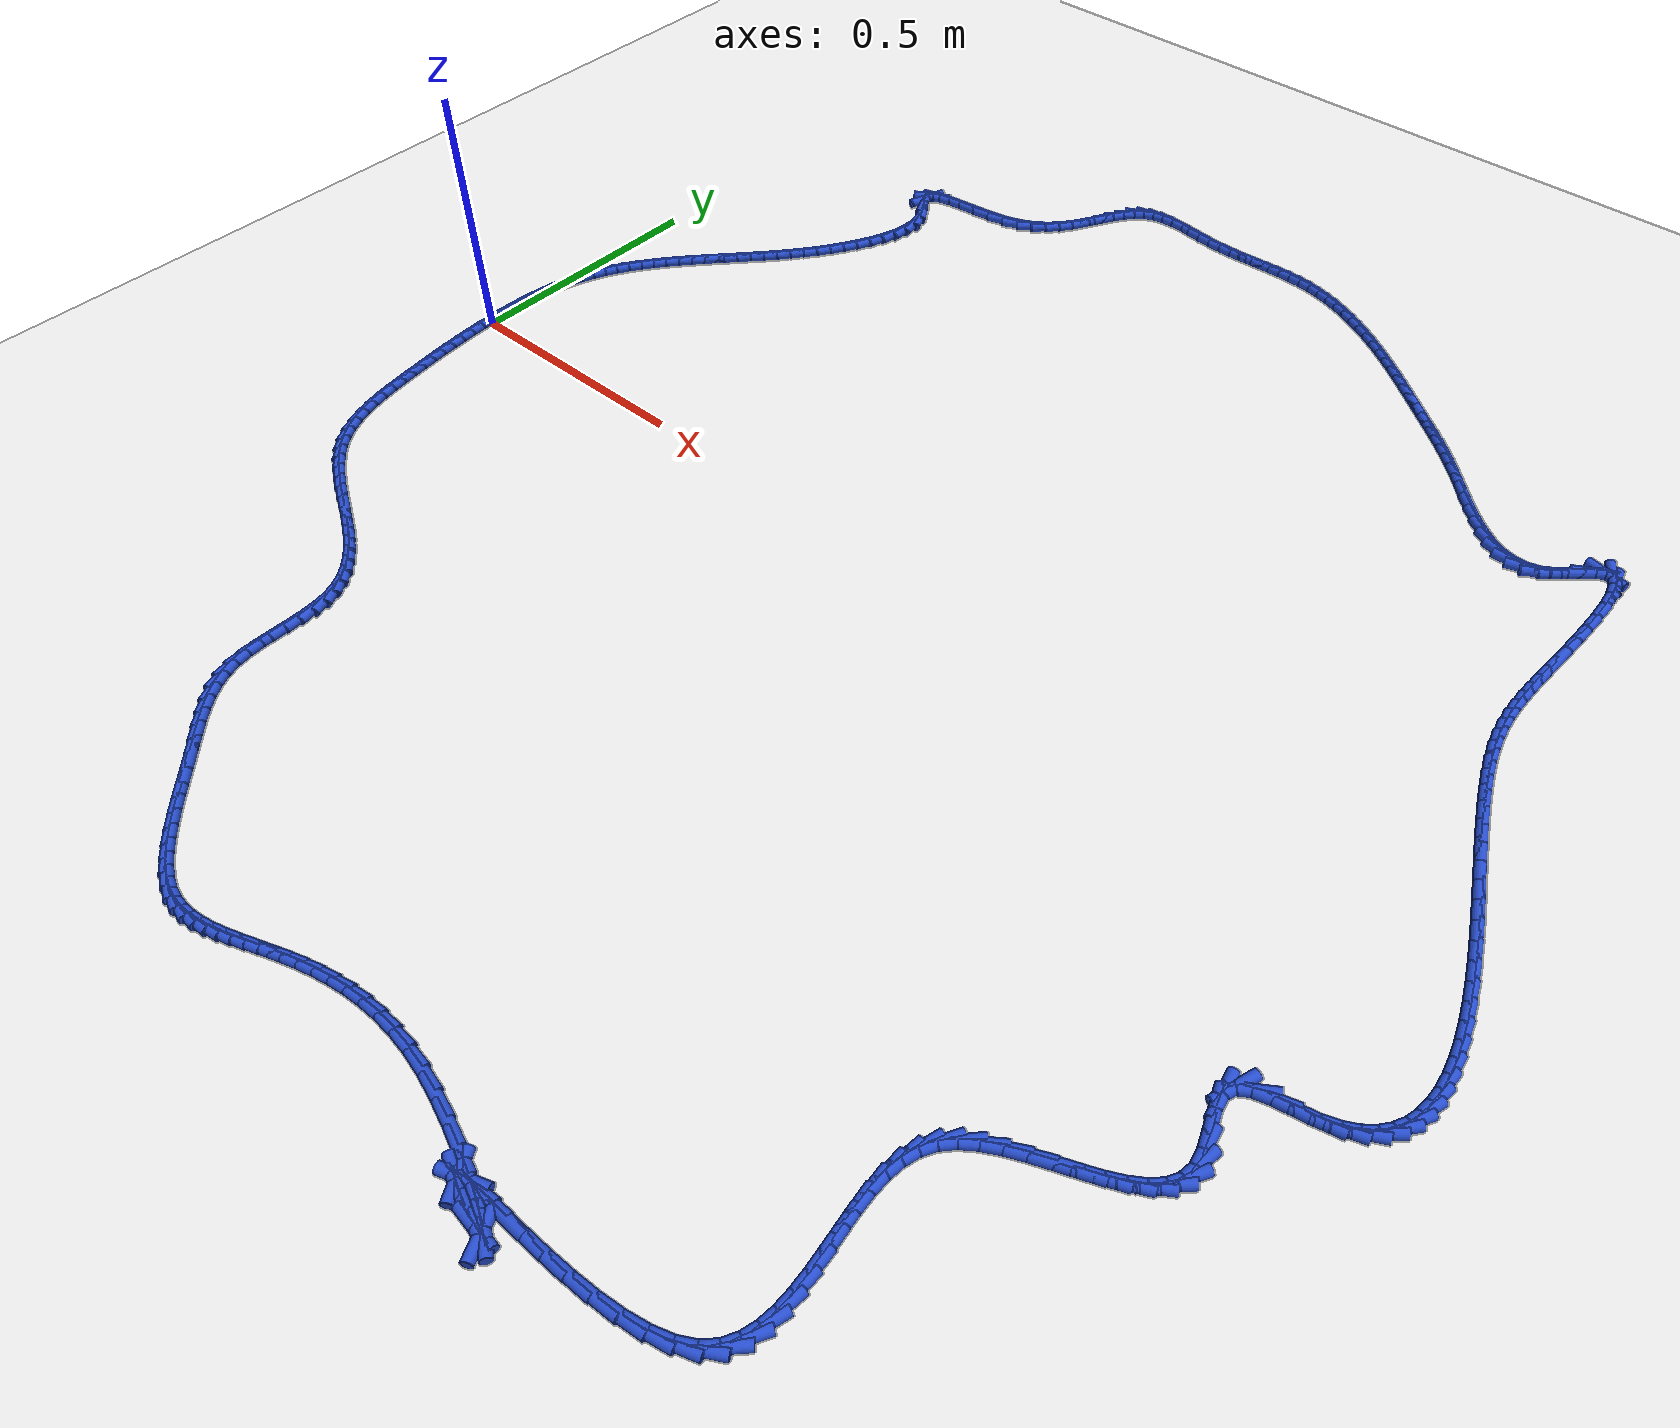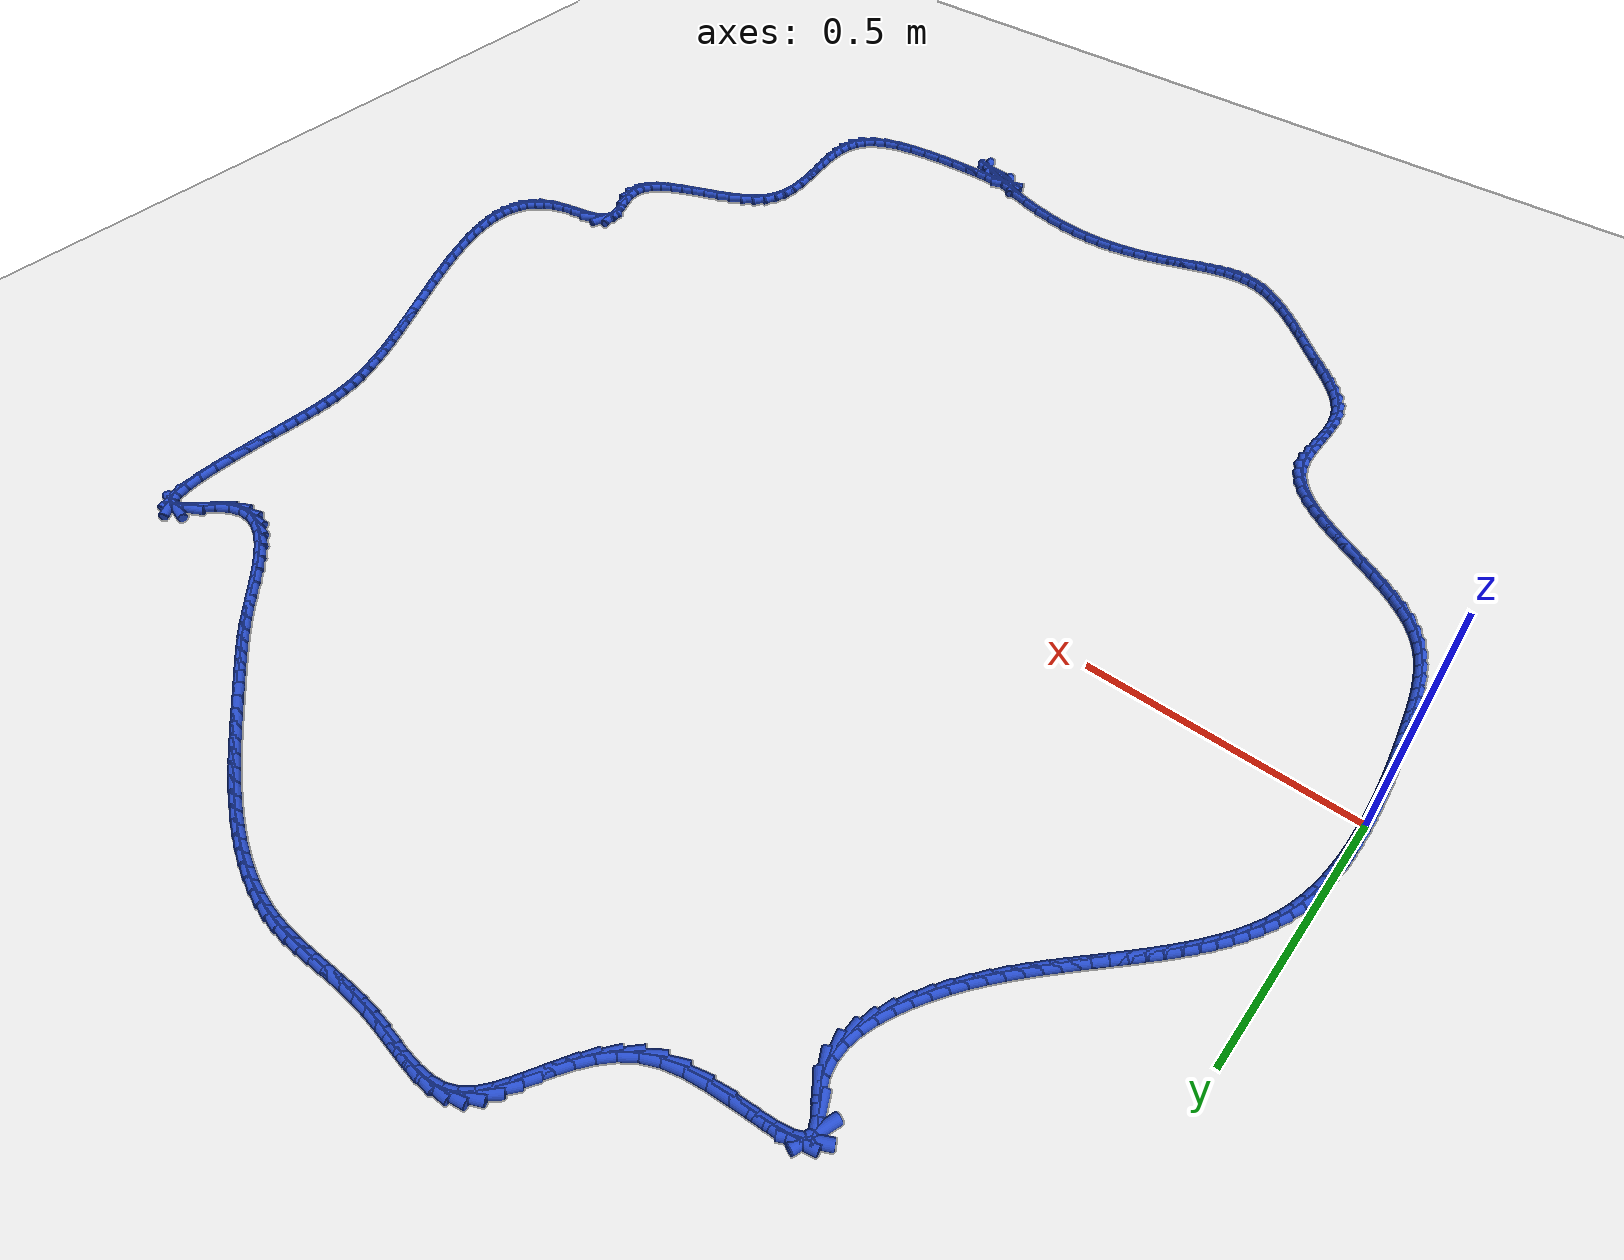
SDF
<sdf version="1.6">
 <world name="default">
  <light name="sun" type="directional">
   <pose>0 0 10 0 -0 0</pose>
   <diffuse>0.8 0.8 0.8 1</diffuse>
   <specular>0.2 0.2 0.2 1</specular>
   <attenuation>
    <range>1000</range>
    <constant>0.9</constant>
    <linear>0.01</linear>
    <quadratic>0.001</quadratic>
   </attenuation>
   <direction>-0.5 0.1 -0.9</direction>
  </light>
  <model name="ground_plane">
   <static>1</static>
   <link name="link">
    <collision name="collision">
     <geometry><plane><normal>0 0 1</normal><size>100 100</size></plane></geometry>
     <surface><friction><ode><mu>100</mu><mu2>50</mu2></ode></friction></surface>
    </collision>
    <visual name="visual">
     <cast_shadows>0</cast_shadows>
     <geometry><plane><normal>0 0 1</normal><size>100 100</size></plane></geometry>
     <material>
      <script><uri>file://media/materials/scripts/gazebo.material</uri><name>Gazebo/WhiteGlow</name></script>
     </material>
    </visual>
   </link>
  </model>
  <gravity>0 0 -9.8</gravity>
  <magnetic_field>6e-06 2.3e-05 -4.2e-05</magnetic_field>
  <atmosphere type="adiabatic"/>
  <physics name="default_physics" default="0" type="ode">
   <max_step_size>0.001</max_step_size>
   <real_time_factor>1</real_time_factor>
   <real_time_update_rate>1000</real_time_update_rate>
  </physics>
  <scene><ambient>0.4 0.4 0.4 1</ambient><background>0.7 0.7 0.7 1</background><shadows>1</shadows></scene>
  <spherical_coordinates>
   <surface_model>EARTH_WGS84</surface_model>
   <latitude_deg>0</latitude_deg>
   <longitude_deg>0</longitude_deg>
   <elevation>0</elevation>
   <heading_deg>0</heading_deg>
  </spherical_coordinates>
  <model name="line">
   <link name="link_0">
    <pose>1.0842021724855044e-17 2.0816681711721685e-17 0.01 0 1.57 -1.5472267662601276</pose>
    <collision name="collision">
     <geometry><cylinder><radius>0.01</radius><length>0.08</length></cylinder></geometry>
    </collision>
    <visual name="visual">
     <material>
      <script><name>Gazebo/Blue</name><uri>file://media/materials/scripts/gazebo.material</uri></script>
     </material>
     <geometry><cylinder><radius>0.01</radius><length>0.08</length></cylinder></geometry>
    </visual>
   </link>
   <link name="link_1">
    <pose>-0.0006464769076090113 0.02742338751018824 0.01 0 1.57 1.5667101648497685</pose>
    <collision name="collision">
     <geometry><cylinder><radius>0.01</radius><length>0.08</length></cylinder></geometry>
    </collision>
    <visual name="visual">
     <material>
      <script><name>Gazebo/Blue</name><uri>file://media/materials/scripts/gazebo.material</uri></script>
     </material>
     <geometry><cylinder><radius>0.01</radius><length>0.08</length></cylinder></geometry>
    </visual>
   </link>
   <link name="link_2">
    <pose>-0.0005337902747085362 0.055000856843833955 0.01 0 1.57 1.5344572373062468</pose>
    <collision name="collision">
     <geometry><cylinder><radius>0.01</radius><length>0.08</length></cylinder></geometry>
    </collision>
    <visual name="visual">
     <material>
      <script><name>Gazebo/Blue</name><uri>file://media/materials/scripts/gazebo.material</uri></script>
     </material>
     <geometry><cylinder><radius>0.01</radius><length>0.08</length></cylinder></geometry>
    </visual>
   </link>
   <link name="link_3">
    <pose>0.00046877436438513354 0.08257786300912566 0.01 0 1.57 1.497151139455644</pose>
    <collision name="collision">
     <geometry><cylinder><radius>0.01</radius><length>0.08</length></cylinder></geometry>
    </collision>
    <visual name="visual">
     <material>
      <script><name>Gazebo/Blue</name><uri>file://media/materials/scripts/gazebo.material</uri></script>
     </material>
     <geometry><cylinder><radius>0.01</radius><length>0.08</length></cylinder></geometry>
    </visual>
   </link>
   <link name="link_4">
    <pose>0.0024919314753556903 0.10999986101425177 0.01 0 1.57 1.4542418787284923</pose>
    <collision name="collision">
     <geometry><cylinder><radius>0.01</radius><length>0.08</length></cylinder></geometry>
    </collision>
    <visual name="visual">
     <material>
      <script><name>Gazebo/Blue</name><uri>file://media/materials/scripts/gazebo.material</uri></script>
     </material>
     <geometry><cylinder><radius>0.01</radius><length>0.08</length></cylinder></geometry>
    </visual>
   </link>
   <link name="link_5">
    <pose>0.005666395523886836 0.13711230586740084 0.01 0 1.57 1.4050965822391075</pose>
    <collision name="collision">
     <geometry><cylinder><radius>0.01</radius><length>0.08</length></cylinder></geometry>
    </collision>
    <visual name="visual">
     <material>
      <script><name>Gazebo/Blue</name><uri>file://media/materials/scripts/gazebo.material</uri></script>
     </material>
     <geometry><cylinder><radius>0.01</radius><length>0.08</length></cylinder></geometry>
    </visual>
   </link>
   <link name="link_6">
    <pose>0.010122880975662265 0.16376065257676137 0.01 0 1.57 1.3490234607499503</pose>
    <collision name="collision">
     <geometry><cylinder><radius>0.01</radius><length>0.08</length></cylinder></geometry>
    </collision>
    <visual name="visual">
     <material>
      <script><name>Gazebo/Blue</name><uri>file://media/materials/scripts/gazebo.material</uri></script>
     </material>
     <geometry><cylinder><radius>0.01</radius><length>0.08</length></cylinder></geometry>
    </visual>
   </link>
   <link name="link_7">
    <pose>0.01599210229636567 0.18979035615052176 0.01 0 1.57 1.2853176665392432</pose>
    <collision name="collision">
     <geometry><cylinder><radius>0.01</radius><length>0.08</length></cylinder></geometry>
    </collision>
    <visual name="visual">
     <material>
      <script><name>Gazebo/Blue</name><uri>file://media/materials/scripts/gazebo.material</uri></script>
     </material>
     <geometry><cylinder><radius>0.01</radius><length>0.08</length></cylinder></geometry>
    </visual>
   </link>
   <link name="link_8">
    <pose>0.02340477395040744 0.21504687159804953 0.01 0 1.57 1.2154745744464812</pose>
    <collision name="collision">
     <geometry><cylinder><radius>0.01</radius><length>0.08</length></cylinder></geometry>
    </collision>
    <visual name="visual">
     <material>
      <script><name>Gazebo/Blue</name><uri>file://media/materials/scripts/gazebo.material</uri></script>
     </material>
     <geometry><cylinder><radius>0.01</radius><length>0.08</length></cylinder></geometry>
    </visual>
   </link>
   <link name="link_9">
    <pose>0.03244760337115915 0.23941640173348774 0.01 0 1.57 1.1480598412882907</pose>
    <collision name="collision">
     <geometry><cylinder><radius>0.01</radius><length>0.08</length></cylinder></geometry>
    </collision>
    <visual name="visual">
     <material>
      <script><name>Gazebo/Blue</name><uri>file://media/materials/scripts/gazebo.material</uri></script>
     </material>
     <geometry><cylinder><radius>0.01</radius><length>0.08</length></cylinder></geometry>
    </visual>
   </link>
   <link name="link_10">
    <pose>0.04303288856855014 0.2629466417727541 0.01 0 1.57 1.0860408025987376</pose>
    <collision name="collision">
     <geometry><cylinder><radius>0.01</radius><length>0.08</length></cylinder></geometry>
    </collision>
    <visual name="visual">
     <material>
      <script><name>Gazebo/Blue</name><uri>file://media/materials/scripts/gazebo.material</uri></script>
     </material>
     <geometry><cylinder><radius>0.01</radius><length>0.08</length></cylinder></geometry>
    </visual>
   </link>
   <link name="link_11">
    <pose>0.055029726157448035 0.28572528876716546 0.01 0 1.57 1.0300897375059677</pose>
    <collision name="collision">
     <geometry><cylinder><radius>0.01</radius><length>0.08</length></cylinder></geometry>
    </collision>
    <visual name="visual">
     <material>
      <script><name>Gazebo/Blue</name><uri>file://media/materials/scripts/gazebo.material</uri></script>
     </material>
     <geometry><cylinder><radius>0.01</radius><length>0.08</length></cylinder></geometry>
    </visual>
   </link>
   <link name="link_12">
    <pose>0.06830721275272042 0.3078400397680383 0.01 0 1.57 0.9806048718350402</pose>
    <collision name="collision">
     <geometry><cylinder><radius>0.01</radius><length>0.08</length></cylinder></geometry>
    </collision>
    <visual name="visual">
     <material>
      <script><name>Gazebo/Blue</name><uri>file://media/materials/scripts/gazebo.material</uri></script>
     </material>
     <geometry><cylinder><radius>0.01</radius><length>0.08</length></cylinder></geometry>
    </visual>
   </link>
   <link name="link_13">
    <pose>0.08273444496923486 0.3293785918266895 0.01 0 1.57 0.9377580595909303</pose>
    <collision name="collision">
     <geometry><cylinder><radius>0.01</radius><length>0.08</length></cylinder></geometry>
    </collision>
    <visual name="visual">
     <material>
      <script><name>Gazebo/Blue</name><uri>file://media/materials/scripts/gazebo.material</uri></script>
     </material>
     <geometry><cylinder><radius>0.01</radius><length>0.08</length></cylinder></geometry>
    </visual>
   </link>
   <link name="link_14">
    <pose>0.09818051942185899 0.3504286419944355 0.01 0 1.57 0.9015536223161307</pose>
    <collision name="collision">
     <geometry><cylinder><radius>0.01</radius><length>0.08</length></cylinder></geometry>
    </collision>
    <visual name="visual">
     <material>
      <script><name>Gazebo/Blue</name><uri>file://media/materials/scripts/gazebo.material</uri></script>
     </material>
     <geometry><cylinder><radius>0.01</radius><length>0.08</length></cylinder></geometry>
    </visual>
   </link>
   <link name="link_15">
    <pose>0.1145145327254604 0.3710778873225931 0.01 0 1.57 0.871885923243283</pose>
    <collision name="collision">
     <geometry><cylinder><radius>0.01</radius><length>0.08</length></cylinder></geometry>
    </collision>
    <visual name="visual">
     <material>
      <script><name>Gazebo/Blue</name><uri>file://media/materials/scripts/gazebo.material</uri></script>
     </material>
     <geometry><cylinder><radius>0.01</radius><length>0.08</length></cylinder></geometry>
    </visual>
   </link>
   <link name="link_16">
    <pose>0.13160558149490664 0.391414024862479 0.01 0 1.57 0.8485885280070876</pose>
    <collision name="collision">
     <geometry><cylinder><radius>0.01</radius><length>0.08</length></cylinder></geometry>
    </collision>
    <visual name="visual">
     <material>
      <script><name>Gazebo/Blue</name><uri>file://media/materials/scripts/gazebo.material</uri></script>
     </material>
     <geometry><cylinder><radius>0.01</radius><length>0.08</length></cylinder></geometry>
    </visual>
   </link>
   <link name="link_17">
    <pose>0.14932276234506534 0.4115247516654098 0.01 0 1.57 0.8314722266942071</pose>
    <collision name="collision">
     <geometry><cylinder><radius>0.01</radius><length>0.08</length></cylinder></geometry>
    </collision>
    <visual name="visual">
     <material>
      <script><name>Gazebo/Blue</name><uri>file://media/materials/scripts/gazebo.material</uri></script>
     </material>
     <geometry><cylinder><radius>0.01</radius><length>0.08</length></cylinder></geometry>
    </visual>
   </link>
   <link name="link_18">
    <pose>0.1675351718908041 0.43149776478270235 0.01 0 1.57 0.8203519997227349</pose>
    <collision name="collision">
     <geometry><cylinder><radius>0.01</radius><length>0.08</length></cylinder></geometry>
    </collision>
    <visual name="visual">
     <material>
      <script><name>Gazebo/Blue</name><uri>file://media/materials/scripts/gazebo.material</uri></script>
     </material>
     <geometry><cylinder><radius>0.01</radius><length>0.08</length></cylinder></geometry>
    </visual>
   </link>
   <link name="link_19">
    <pose>0.18611190674699052 0.45142076126567304 0.01 0 1.57 0.815064344698585</pose>
    <collision name="collision">
     <geometry><cylinder><radius>0.01</radius><length>0.08</length></cylinder></geometry>
    </collision>
    <visual name="visual">
     <material>
      <script><name>Gazebo/Blue</name><uri>file://media/materials/scripts/gazebo.material</uri></script>
     </material>
     <geometry><cylinder><radius>0.01</radius><length>0.08</length></cylinder></geometry>
    </visual>
   </link>
   <link name="link_20">
    <pose>0.20492206352849224 0.47138143816563893 0.01 0 1.57 0.8154767114710165</pose>
    <collision name="collision">
     <geometry><cylinder><radius>0.01</radius><length>0.08</length></cylinder></geometry>
    </collision>
    <visual name="visual">
     <material>
      <script><name>Gazebo/Blue</name><uri>file://media/materials/scripts/gazebo.material</uri></script>
     </material>
     <geometry><cylinder><radius>0.01</radius><length>0.08</length></cylinder></geometry>
    </visual>
   </link>
   <link name="link_21">
    <pose>0.22383473885017674 0.4914674925339162 0.01 0 1.57 0.8214905726017478</pose>
    <collision name="collision">
     <geometry><cylinder><radius>0.01</radius><length>0.08</length></cylinder></geometry>
    </collision>
    <visual name="visual">
     <material>
      <script><name>Gazebo/Blue</name><uri>file://media/materials/scripts/gazebo.material</uri></script>
     </material>
     <geometry><cylinder><radius>0.01</radius><length>0.08</length></cylinder></geometry>
    </visual>
   </link>
   <link name="link_22">
    <pose>0.24271902932691167 0.511766621421822 0.01 0 1.57 0.8330392102226798</pose>
    <collision name="collision">
     <geometry><cylinder><radius>0.01</radius><length>0.08</length></cylinder></geometry>
    </collision>
    <visual name="visual">
     <material>
      <script><name>Gazebo/Blue</name><uri>file://media/materials/scripts/gazebo.material</uri></script>
     </material>
     <geometry><cylinder><radius>0.01</radius><length>0.08</length></cylinder></geometry>
    </visual>
   </link>
   <link name="link_23">
    <pose>0.26144403157356455 0.5323665218806728 0.01 0 1.57 0.8500808257828767</pose>
    <collision name="collision">
     <geometry><cylinder><radius>0.01</radius><length>0.08</length></cylinder></geometry>
    </collision>
    <visual name="visual">
     <material>
      <script><name>Gazebo/Blue</name><uri>file://media/materials/scripts/gazebo.material</uri></script>
     </material>
     <geometry><cylinder><radius>0.01</radius><length>0.08</length></cylinder></geometry>
    </visual>
   </link>
   <link name="link_24">
    <pose>0.27987884220500314 0.5533548909617851 0.01 0 1.57 0.8725871944044229</pose>
    <collision name="collision">
     <geometry><cylinder><radius>0.01</radius><length>0.08</length></cylinder></geometry>
    </collision>
    <visual name="visual">
     <material>
      <script><name>Gazebo/Blue</name><uri>file://media/materials/scripts/gazebo.material</uri></script>
     </material>
     <geometry><cylinder><radius>0.01</radius><length>0.08</length></cylinder></geometry>
    </visual>
   </link>
   <link name="link_25">
    <pose>0.2978925578360949 0.5748194257164759 0.01 0 1.57 0.9005278743627724</pose>
    <collision name="collision">
     <geometry><cylinder><radius>0.01</radius><length>0.08</length></cylinder></geometry>
    </collision>
    <visual name="visual">
     <material>
      <script><name>Gazebo/Blue</name><uri>file://media/materials/scripts/gazebo.material</uri></script>
     </material>
     <geometry><cylinder><radius>0.01</radius><length>0.08</length></cylinder></geometry>
    </visual>
   </link>
   <link name="link_26">
    <pose>0.31535427508170755 0.5968478231960617 0.01 0 1.57 0.9338500247431556</pose>
    <collision name="collision">
     <geometry><cylinder><radius>0.01</radius><length>0.08</length></cylinder></geometry>
    </collision>
    <visual name="visual">
     <material>
      <script><name>Gazebo/Blue</name><uri>file://media/materials/scripts/gazebo.material</uri></script>
     </material>
     <geometry><cylinder><radius>0.01</radius><length>0.08</length></cylinder></geometry>
    </visual>
   </link>
   <link name="link_27">
    <pose>0.3321330905567085 0.6195277804518591 0.01 0 1.57 0.9724542643620521</pose>
    <collision name="collision">
     <geometry><cylinder><radius>0.01</radius><length>0.08</length></cylinder></geometry>
    </collision>
    <visual name="visual">
     <material>
      <script><name>Gazebo/Blue</name><uri>file://media/materials/scripts/gazebo.material</uri></script>
     </material>
     <geometry><cylinder><radius>0.01</radius><length>0.08</length></cylinder></geometry>
    </visual>
   </link>
   <link name="link_28">
    <pose>0.34809810087596554 0.6429469945351851 0.01 0 1.57 1.0161677870229466</pose>
    <collision name="collision">
     <geometry><cylinder><radius>0.01</radius><length>0.08</length></cylinder></geometry>
    </collision>
    <visual name="visual">
     <material>
      <script><name>Gazebo/Blue</name><uri>file://media/materials/scripts/gazebo.material</uri></script>
     </material>
     <geometry><cylinder><radius>0.01</radius><length>0.08</length></cylinder></geometry>
    </visual>
   </link>
   <link name="link_29">
    <pose>0.36311840265434614 0.667193162497356 0.01 0 1.57 1.0647171182484148</pose>
    <collision name="collision">
     <geometry><cylinder><radius>0.01</radius><length>0.08</length></cylinder></geometry>
    </collision>
    <visual name="visual">
     <material>
      <script><name>Gazebo/Blue</name><uri>file://media/materials/scripts/gazebo.material</uri></script>
     </material>
     <geometry><cylinder><radius>0.01</radius><length>0.08</length></cylinder></geometry>
    </visual>
   </link>
   <link name="link_30">
    <pose>0.37706309250671777 0.6923539813896886 0.01 0 1.57 1.118040622239205</pose>
    <collision name="collision">
     <geometry><cylinder><radius>0.01</radius><length>0.08</length></cylinder></geometry>
    </collision>
    <visual name="visual">
     <material>
      <script><name>Gazebo/Blue</name><uri>file://media/materials/scripts/gazebo.material</uri></script>
     </material>
     <geometry><cylinder><radius>0.01</radius><length>0.08</length></cylinder></geometry>
    </visual>
   </link>
   <link name="link_31">
    <pose>0.3897865844151637 0.7185093396019593 0.01 0 1.57 1.1857493874936564</pose>
    <collision name="collision">
     <geometry><cylinder><radius>0.01</radius><length>0.08</length></cylinder></geometry>
    </collision>
    <visual name="visual">
     <material>
      <script><name>Gazebo/Blue</name><uri>file://media/materials/scripts/gazebo.material</uri></script>
     </material>
     <geometry><cylinder><radius>0.01</radius><length>0.08</length></cylinder></geometry>
    </visual>
   </link>
   <link name="link_32">
    <pose>0.4007339532052216 0.7455214267654455 0.01 0 1.57 1.2821522923453965</pose>
    <collision name="collision">
     <geometry><cylinder><radius>0.01</radius><length>0.08</length></cylinder></geometry>
    </collision>
    <visual name="visual">
     <material>
      <script><name>Gazebo/Blue</name><uri>file://media/materials/scripts/gazebo.material</uri></script>
     </material>
     <geometry><cylinder><radius>0.01</radius><length>0.08</length></cylinder></geometry>
    </visual>
   </link>
   <link name="link_33">
    <pose>0.40889667317359285 0.7730111942365051 0.01 0 1.57 1.4144811588258666</pose>
    <collision name="collision">
     <geometry><cylinder><radius>0.01</radius><length>0.08</length></cylinder></geometry>
    </collision>
    <visual name="visual">
     <material>
      <script><name>Gazebo/Blue</name><uri>file://media/materials/scripts/gazebo.material</uri></script>
     </material>
     <geometry><cylinder><radius>0.01</radius><length>0.08</length></cylinder></geometry>
    </visual>
   </link>
   <link name="link_34">
    <pose>0.41324265444611136 0.8005870612434041 0.01 0 1.57 -1.5523590988592881</pose>
    <collision name="collision">
     <geometry><cylinder><radius>0.01</radius><length>0.08</length></cylinder></geometry>
    </collision>
    <visual name="visual">
     <material>
      <script><name>Gazebo/Blue</name><uri>file://media/materials/scripts/gazebo.material</uri></script>
     </material>
     <geometry><cylinder><radius>0.01</radius><length>0.08</length></cylinder></geometry>
    </visual>
   </link>
   <link name="link_35">
    <pose>0.4127398071486105 0.8278574470144081 0.01 0 1.57 -1.3350318853179919</pose>
    <collision name="collision">
     <geometry><cylinder><radius>0.01</radius><length>0.08</length></cylinder></geometry>
    </collision>
    <visual name="visual">
     <material>
      <script><name>Gazebo/Blue</name><uri>file://media/materials/scripts/gazebo.material</uri></script>
     </material>
     <geometry><cylinder><radius>0.01</radius><length>0.08</length></cylinder></geometry>
    </visual>
   </link>
   <link name="link_36">
    <pose>0.40635604140692444 0.854430770777783 0.01 0 1.57 -1.0912896111527306</pose>
    <collision name="collision">
     <geometry><cylinder><radius>0.01</radius><length>0.08</length></cylinder></geometry>
    </collision>
    <visual name="visual">
     <material>
      <script><name>Gazebo/Blue</name><uri>file://media/materials/scripts/gazebo.material</uri></script>
     </material>
     <geometry><cylinder><radius>0.01</radius><length>0.08</length></cylinder></geometry>
    </visual>
   </link>
   <link name="link_37">
    <pose>0.3931087761935838 0.8799070635571985 0.01 0 1.57 -0.9489355991953212</pose>
    <collision name="collision">
     <geometry><cylinder><radius>0.01</radius><length>0.08</length></cylinder></geometry>
    </collision>
    <visual name="visual">
     <material>
      <script><name>Gazebo/Blue</name><uri>file://media/materials/scripts/gazebo.material</uri></script>
     </material>
     <geometry><cylinder><radius>0.01</radius><length>0.08</length></cylinder></geometry>
    </visual>
   </link>
   <link name="link_38">
    <pose>0.37646228924891295 0.9031329322180112 0.01 0 1.57 -1.1241383825546074</pose>
    <collision name="collision">
     <geometry><cylinder><radius>0.01</radius><length>0.08</length></cylinder></geometry>
    </collision>
    <visual name="visual">
     <material>
      <script><name>Gazebo/Blue</name><uri>file://media/materials/scripts/gazebo.material</uri></script>
     </material>
     <geometry><cylinder><radius>0.01</radius><length>0.08</length></cylinder></geometry>
    </visual>
   </link>
   <link name="link_39">
    <pose>0.3675837820433815 0.9216707678445553 0.01 0 1.57 1.2415030645651493</pose>
    <collision name="collision">
     <geometry><cylinder><radius>0.01</radius><length>0.08</length></cylinder></geometry>
    </collision>
    <visual name="visual">
     <material>
      <script><name>Gazebo/Blue</name><uri>file://media/materials/scripts/gazebo.material</uri></script>
     </material>
     <geometry><cylinder><radius>0.01</radius><length>0.08</length></cylinder></geometry>
    </visual>
   </link>
   <link name="link_40">
    <pose>0.3720297221334209 0.9346806580659512 0.01 0 1.57 0.5014006837821909</pose>
    <collision name="collision">
     <geometry><cylinder><radius>0.01</radius><length>0.08</length></cylinder></geometry>
    </collision>
    <visual name="visual">
     <material>
      <script><name>Gazebo/Blue</name><uri>file://media/materials/scripts/gazebo.material</uri></script>
     </material>
     <geometry><cylinder><radius>0.01</radius><length>0.08</length></cylinder></geometry>
    </visual>
   </link>
   <link name="link_41">
    <pose>0.3878479478251402 0.9433509850057565 0.01 0 1.57 0.22327820769206896</pose>
    <collision name="collision">
     <geometry><cylinder><radius>0.01</radius><length>0.08</length></cylinder></geometry>
    </collision>
    <visual name="visual">
     <material>
      <script><name>Gazebo/Blue</name><uri>file://media/materials/scripts/gazebo.material</uri></script>
     </material>
     <geometry><cylinder><radius>0.01</radius><length>0.08</length></cylinder></geometry>
    </visual>
   </link>
   <link name="link_42">
    <pose>0.41266075355690574 0.9489850822993577 0.01 0 1.57 0.12349311993638151</pose>
    <collision name="collision">
     <geometry><cylinder><radius>0.01</radius><length>0.08</length></cylinder></geometry>
    </collision>
    <visual name="visual">
     <material>
      <script><name>Gazebo/Blue</name><uri>file://media/materials/scripts/gazebo.material</uri></script>
     </material>
     <geometry><cylinder><radius>0.01</radius><length>0.08</length></cylinder></geometry>
    </visual>
   </link>
   <link name="link_43">
    <pose>0.4440904337670829 0.952886283582141 0.01 0 1.57 0.09702411259552497</pose>
    <collision name="collision">
     <geometry><cylinder><radius>0.01</radius><length>0.08</length></cylinder></geometry>
    </collision>
    <visual name="visual">
     <material>
      <script><name>Gazebo/Blue</name><uri>file://media/materials/scripts/gazebo.material</uri></script>
     </material>
     <geometry><cylinder><radius>0.01</radius><length>0.08</length></cylinder></geometry>
    </visual>
   </link>
   <link name="link_44">
    <pose>0.4797592828940381 0.9563579224894921 0.01 0 1.57 0.11527073697474434</pose>
    <collision name="collision">
     <geometry><cylinder><radius>0.01</radius><length>0.08</length></cylinder></geometry>
    </collision>
    <visual name="visual">
     <material>
      <script><name>Gazebo/Blue</name><uri>file://media/materials/scripts/gazebo.material</uri></script>
     </material>
     <geometry><cylinder><radius>0.01</radius><length>0.08</length></cylinder></geometry>
    </visual>
   </link>
   <link name="link_45">
    <pose>0.5172895953761372 0.9607033326567984 0.01 0 1.57 0.17442643282115197</pose>
    <collision name="collision">
     <geometry><cylinder><radius>0.01</radius><length>0.08</length></cylinder></geometry>
    </collision>
    <visual name="visual">
     <material>
      <script><name>Gazebo/Blue</name><uri>file://media/materials/scripts/gazebo.material</uri></script>
     </material>
     <geometry><cylinder><radius>0.01</radius><length>0.08</length></cylinder></geometry>
    </visual>
   </link>
   <link name="link_46">
    <pose>0.5543036656517455 0.9672258477194454 0.01 0 1.57 0.2851778676747113</pose>
    <collision name="collision">
     <geometry><cylinder><radius>0.01</radius><length>0.08</length></cylinder></geometry>
    </collision>
    <visual name="visual">
     <material>
      <script><name>Gazebo/Blue</name><uri>file://media/materials/scripts/gazebo.material</uri></script>
     </material>
     <geometry><cylinder><radius>0.01</radius><length>0.08</length></cylinder></geometry>
    </visual>
   </link>
   <link name="link_47">
    <pose>0.58842378815923 0.97722880131282 0.01 0 1.57 0.4610184953335223</pose>
    <collision name="collision">
     <geometry><cylinder><radius>0.01</radius><length>0.08</length></cylinder></geometry>
    </collision>
    <visual name="visual">
     <material>
      <script><name>Gazebo/Blue</name><uri>file://media/materials/scripts/gazebo.material</uri></script>
     </material>
     <geometry><cylinder><radius>0.01</radius><length>0.08</length></cylinder></geometry>
    </visual>
   </link>
   <link name="link_48">
    <pose>0.6176505555155068 0.9917462602515781 0.01 0 1.57 0.6491756528381208</pose>
    <collision name="collision">
     <geometry><cylinder><radius>0.01</radius><length>0.08</length></cylinder></geometry>
    </collision>
    <visual name="visual">
     <material>
      <script><name>Gazebo/Blue</name><uri>file://media/materials/scripts/gazebo.material</uri></script>
     </material>
     <geometry><cylinder><radius>0.01</radius><length>0.08</length></cylinder></geometry>
    </visual>
   </link>
   <link name="link_49">
    <pose>0.6421037404690992 1.0103038915511022 0.01 0 1.57 0.8105893672730653</pose>
    <collision name="collision">
     <geometry><cylinder><radius>0.01</radius><length>0.08</length></cylinder></geometry>
    </collision>
    <visual name="visual">
     <material>
      <script><name>Gazebo/Blue</name><uri>file://media/materials/scripts/gazebo.material</uri></script>
     </material>
     <geometry><cylinder><radius>0.01</radius><length>0.08</length></cylinder></geometry>
    </visual>
   </link>
   <link name="link_50">
    <pose>0.6626406088276664 1.0319024260187697 0.01 0 1.57 0.9341297473582626</pose>
    <collision name="collision">
     <geometry><cylinder><radius>0.01</radius><length>0.08</length></cylinder></geometry>
    </collision>
    <visual name="visual">
     <material>
      <script><name>Gazebo/Blue</name><uri>file://media/materials/scripts/gazebo.material</uri></script>
     </material>
     <geometry><cylinder><radius>0.01</radius><length>0.08</length></cylinder></geometry>
    </visual>
   </link>
   <link name="link_51">
    <pose>0.6801191733727217 1.0555420627774648 0.01 0 1.57 1.016500620614596</pose>
    <collision name="collision">
     <geometry><cylinder><radius>0.01</radius><length>0.08</length></cylinder></geometry>
    </collision>
    <visual name="visual">
     <material>
      <script><name>Gazebo/Blue</name><uri>file://media/materials/scripts/gazebo.material</uri></script>
     </material>
     <geometry><cylinder><radius>0.01</radius><length>0.08</length></cylinder></geometry>
    </visual>
   </link>
   <link name="link_52">
    <pose>0.6953974468857791 1.0802230009500728 0.01 0 1.57 1.0574970945589088</pose>
    <collision name="collision">
     <geometry><cylinder><radius>0.01</radius><length>0.08</length></cylinder></geometry>
    </collision>
    <visual name="visual">
     <material>
      <script><name>Gazebo/Blue</name><uri>file://media/materials/scripts/gazebo.material</uri></script>
     </material>
     <geometry><cylinder><radius>0.01</radius><length>0.08</length></cylinder></geometry>
    </visual>
   </link>
   <link name="link_53">
    <pose>0.7093334421483519 1.1049454396594784 0.01 0 1.57 1.055712970119861</pose>
    <collision name="collision">
     <geometry><cylinder><radius>0.01</radius><length>0.08</length></cylinder></geometry>
    </collision>
    <visual name="visual">
     <material>
      <script><name>Gazebo/Blue</name><uri>file://media/materials/scripts/gazebo.material</uri></script>
     </material>
     <geometry><cylinder><radius>0.01</radius><length>0.08</length></cylinder></geometry>
    </visual>
   </link>
   <link name="link_54">
    <pose>0.7227851719419539 1.1287095780285663 0.01 0 1.57 1.0057365586673044</pose>
    <collision name="collision">
     <geometry><cylinder><radius>0.01</radius><length>0.08</length></cylinder></geometry>
    </collision>
    <visual name="visual">
     <material>
      <script><name>Gazebo/Blue</name><uri>file://media/materials/scripts/gazebo.material</uri></script>
     </material>
     <geometry><cylinder><radius>0.01</radius><length>0.08</length></cylinder></geometry>
    </visual>
   </link>
   <link name="link_55">
    <pose>0.7366106490480984 1.150515615180221 0.01 0 1.57 0.8967438967059834</pose>
    <collision name="collision">
     <geometry><cylinder><radius>0.01</radius><length>0.08</length></cylinder></geometry>
    </collision>
    <visual name="visual">
     <material>
      <script><name>Gazebo/Blue</name><uri>file://media/materials/scripts/gazebo.material</uri></script>
     </material>
     <geometry><cylinder><radius>0.01</radius><length>0.08</length></cylinder></geometry>
    </visual>
   </link>
   <link name="link_56">
    <pose>0.7516678862482992 1.1693637502373275 0.01 0 1.57 0.715078651477741</pose>
    <collision name="collision">
     <geometry><cylinder><radius>0.01</radius><length>0.08</length></cylinder></geometry>
    </collision>
    <visual name="visual">
     <material>
      <script><name>Gazebo/Blue</name><uri>file://media/materials/scripts/gazebo.material</uri></script>
     </material>
     <geometry><cylinder><radius>0.01</radius><length>0.08</length></cylinder></geometry>
    </visual>
   </link>
   <link name="link_57">
    <pose>0.7688148963240695 1.1842541823227708 0.01 0 1.57 0.45997879157687427</pose>
    <collision name="collision">
     <geometry><cylinder><radius>0.01</radius><length>0.08</length></cylinder></geometry>
    </collision>
    <visual name="visual">
     <material>
      <script><name>Gazebo/Blue</name><uri>file://media/materials/scripts/gazebo.material</uri></script>
     </material>
     <geometry><cylinder><radius>0.01</radius><length>0.08</length></cylinder></geometry>
    </visual>
   </link>
   <link name="link_58">
    <pose>0.7888980002489249 1.1942038009639948 0.01 0 1.57 0.2064298014438927</pose>
    <collision name="collision">
     <geometry><cylinder><radius>0.01</radius><length>0.08</length></cylinder></geometry>
    </collision>
    <visual name="visual">
     <material>
      <script><name>Gazebo/Blue</name><uri>file://media/materials/scripts/gazebo.material</uri></script>
     </material>
     <geometry><cylinder><radius>0.01</radius><length>0.08</length></cylinder></geometry>
    </visual>
   </link>
   <link name="link_59">
    <pose>0.8121696972500413 1.199077193938701 0.01 0 1.57 0.034578090407673005</pose>
    <collision name="collision">
     <geometry><cylinder><radius>0.01</radius><length>0.08</length></cylinder></geometry>
    </collision>
    <visual name="visual">
     <material>
      <script><name>Gazebo/Blue</name><uri>file://media/materials/scripts/gazebo.material</uri></script>
     </material>
     <geometry><cylinder><radius>0.01</radius><length>0.08</length></cylinder></geometry>
    </visual>
   </link>
   <link name="link_60">
    <pose>0.8380191586483201 1.1999713753546453 0.01 0 1.57 -0.0680423082417495</pose>
    <collision name="collision">
     <geometry><cylinder><radius>0.01</radius><length>0.08</length></cylinder></geometry>
    </collision>
    <visual name="visual">
     <material>
      <script><name>Gazebo/Blue</name><uri>file://media/materials/scripts/gazebo.material</uri></script>
     </material>
     <geometry><cylinder><radius>0.01</radius><length>0.08</length></cylinder></geometry>
    </visual>
   </link>
   <link name="link_61">
    <pose>0.8657675852990155 1.198080389186129 0.01 0 1.57 -0.119628972244039</pose>
    <collision name="collision">
     <geometry><cylinder><radius>0.01</radius><length>0.08</length></cylinder></geometry>
    </collision>
    <visual name="visual">
     <material>
      <script><name>Gazebo/Blue</name><uri>file://media/materials/scripts/gazebo.material</uri></script>
     </material>
     <geometry><cylinder><radius>0.01</radius><length>0.08</length></cylinder></geometry>
    </visual>
   </link>
   <link name="link_62">
    <pose>0.894736178057381 1.1945982794074512 0.01 0 1.57 -0.130704145717752</pose>
    <collision name="collision">
     <geometry><cylinder><radius>0.01</radius><length>0.08</length></cylinder></geometry>
    </collision>
    <visual name="visual">
     <material>
      <script><name>Gazebo/Blue</name><uri>file://media/materials/scripts/gazebo.material</uri></script>
     </material>
     <geometry><cylinder><radius>0.01</radius><length>0.08</length></cylinder></geometry>
    </visual>
   </link>
   <link name="link_63">
    <pose>0.9242461377786714 1.1907190899929132 0.01 0 1.57 -0.1046156095233645</pose>
    <collision name="collision">
     <geometry><cylinder><radius>0.01</radius><length>0.08</length></cylinder></geometry>
    </collision>
    <visual name="visual">
     <material>
      <script><name>Gazebo/Blue</name><uri>file://media/materials/scripts/gazebo.material</uri></script>
     </material>
     <geometry><cylinder><radius>0.01</radius><length>0.08</length></cylinder></geometry>
    </visual>
   </link>
   <link name="link_64">
    <pose>0.9536195562925613 1.187634912174922 0.01 0 1.57 -0.0537991804581383</pose>
    <collision name="collision">
     <geometry><cylinder><radius>0.01</radius><length>0.08</length></cylinder></geometry>
    </collision>
    <visual name="visual">
     <material>
      <script><name>Gazebo/Blue</name><uri>file://media/materials/scripts/gazebo.material</uri></script>
     </material>
     <geometry><cylinder><radius>0.01</radius><length>0.08</length></cylinder></geometry>
    </visual>
   </link>
   <link name="link_65">
    <pose>0.9823847419558119 1.1860858739848947 0.01 0 1.57 -0.010707895062189367</pose>
    <collision name="collision">
     <geometry><cylinder><radius>0.01</radius><length>0.08</length></cylinder></geometry>
    </collision>
    <visual name="visual">
     <material>
      <script><name>Gazebo/Blue</name><uri>file://media/materials/scripts/gazebo.material</uri></script>
     </material>
     <geometry><cylinder><radius>0.01</radius><length>0.08</length></cylinder></geometry>
    </visual>
   </link>
   <link name="link_66">
    <pose>1.010538916062371 1.1857843905203118 0.01 0 1.57 0.01870388746321642</pose>
    <collision name="collision">
     <geometry><cylinder><radius>0.01</radius><length>0.08</length></cylinder></geometry>
    </collision>
    <visual name="visual">
     <material>
      <script><name>Gazebo/Blue</name><uri>file://media/materials/scripts/gazebo.material</uri></script>
     </material>
     <geometry><cylinder><radius>0.01</radius><length>0.08</length></cylinder></geometry>
    </visual>
   </link>
   <link name="link_67">
    <pose>1.0381441361978527 1.1863007756691304 0.01 0 1.57 0.0333439631039731</pose>
    <collision name="collision">
     <geometry><cylinder><radius>0.01</radius><length>0.08</length></cylinder></geometry>
    </collision>
    <visual name="visual">
     <material>
      <script><name>Gazebo/Blue</name><uri>file://media/materials/scripts/gazebo.material</uri></script>
     </material>
     <geometry><cylinder><radius>0.01</radius><length>0.08</length></cylinder></geometry>
    </visual>
   </link>
   <link name="link_68">
    <pose>1.0652624599478735 1.1872053433193077 0.01 0 1.57 0.03232112575038664</pose>
    <collision name="collision">
     <geometry><cylinder><radius>0.01</radius><length>0.08</length></cylinder></geometry>
    </collision>
    <visual name="visual">
     <material>
      <script><name>Gazebo/Blue</name><uri>file://media/materials/scripts/gazebo.material</uri></script>
     </material>
     <geometry><cylinder><radius>0.01</radius><length>0.08</length></cylinder></geometry>
    </visual>
   </link>
   <link name="link_69">
    <pose>1.0919559448980485 1.188068407358801 0.01 0 1.57 0.014881690648698268</pose>
    <collision name="collision">
     <geometry><cylinder><radius>0.01</radius><length>0.08</length></cylinder></geometry>
    </collision>
    <visual name="visual">
     <material>
      <script><name>Gazebo/Blue</name><uri>file://media/materials/scripts/gazebo.material</uri></script>
     </material>
     <geometry><cylinder><radius>0.01</radius><length>0.08</length></cylinder></geometry>
    </visual>
   </link>
   <link name="link_70">
    <pose>1.1182866486339924 1.1884602816755672 0.01 0 1.57 -0.019551941805255272</pose>
    <collision name="collision">
     <geometry><cylinder><radius>0.01</radius><length>0.08</length></cylinder></geometry>
    </collision>
    <visual name="visual">
     <material>
      <script><name>Gazebo/Blue</name><uri>file://media/materials/scripts/gazebo.material</uri></script>
     </material>
     <geometry><cylinder><radius>0.01</radius><length>0.08</length></cylinder></geometry>
    </visual>
   </link>
   <link name="link_71">
    <pose>1.1443166287413213 1.1879512801575636 0.01 0 1.57 -0.07120434077144835</pose>
    <collision name="collision">
     <geometry><cylinder><radius>0.01</radius><length>0.08</length></cylinder></geometry>
    </collision>
    <visual name="visual">
     <material>
      <script><name>Gazebo/Blue</name><uri>file://media/materials/scripts/gazebo.material</uri></script>
     </material>
     <geometry><cylinder><radius>0.01</radius><length>0.08</length></cylinder></geometry>
    </visual>
   </link>
   <link name="link_72">
    <pose>1.1701079428056502 1.1861117166927473 0.01 0 1.57 -0.13897435776798897</pose>
    <collision name="collision">
     <geometry><cylinder><radius>0.01</radius><length>0.08</length></cylinder></geometry>
    </collision>
    <visual name="visual">
     <material>
      <script><name>Gazebo/Blue</name><uri>file://media/materials/scripts/gazebo.material</uri></script>
     </material>
     <geometry><cylinder><radius>0.01</radius><length>0.08</length></cylinder></geometry>
    </visual>
   </link>
   <link name="link_73">
    <pose>1.1957202697943599 1.182529165937361 0.01 0 1.57 -0.21064683466283354</pose>
    <collision name="collision">
     <geometry><cylinder><radius>0.01</radius><length>0.08</length></cylinder></geometry>
    </collision>
    <visual name="visual">
     <material>
      <script><name>Gazebo/Blue</name><uri>file://media/materials/scripts/gazebo.material</uri></script>
     </material>
     <geometry><cylinder><radius>0.01</radius><length>0.08</length></cylinder></geometry>
    </visual>
   </link>
   <link name="link_74">
    <pose>1.221172526899955 1.1770869959376105 0.01 0 1.57 -0.27639310832509073</pose>
    <collision name="collision">
     <geometry><cylinder><radius>0.01</radius><length>0.08</length></cylinder></geometry>
    </collision>
    <visual name="visual">
     <material>
      <script><name>Gazebo/Blue</name><uri>file://media/materials/scripts/gazebo.material</uri></script>
     </material>
     <geometry><cylinder><radius>0.01</radius><length>0.08</length></cylinder></geometry>
    </visual>
   </link>
   <link name="link_75">
    <pose>1.2464493784059067 1.1699171356551743 0.01 0 1.57 -0.33589795598405275</pose>
    <collision name="collision">
     <geometry><cylinder><radius>0.01</radius><length>0.08</length></cylinder></geometry>
    </collision>
    <visual name="visual">
     <material>
      <script><name>Gazebo/Blue</name><uri>file://media/materials/scripts/gazebo.material</uri></script>
     </material>
     <geometry><cylinder><radius>0.01</radius><length>0.08</length></cylinder></geometry>
    </visual>
   </link>
   <link name="link_76">
    <pose>1.2715344241142106 1.161159238607028 0.01 0 1.57 -0.38933039295243377</pose>
    <collision name="collision">
     <geometry><cylinder><radius>0.01</radius><length>0.08</length></cylinder></geometry>
    </collision>
    <visual name="visual">
     <material>
      <script><name>Gazebo/Blue</name><uri>file://media/materials/scripts/gazebo.material</uri></script>
     </material>
     <geometry><cylinder><radius>0.01</radius><length>0.08</length></cylinder></geometry>
    </visual>
   </link>
   <link name="link_77">
    <pose>1.2964112638268621 1.1509529583101479 0.01 0 1.57 -0.4369813335193183</pose>
    <collision name="collision">
     <geometry><cylinder><radius>0.01</radius><length>0.08</length></cylinder></geometry>
    </collision>
    <visual name="visual">
     <material>
      <script><name>Gazebo/Blue</name><uri>file://media/materials/scripts/gazebo.material</uri></script>
     </material>
     <geometry><cylinder><radius>0.01</radius><length>0.08</length></cylinder></geometry>
    </visual>
   </link>
   <link name="link_78">
    <pose>1.3210634973458575 1.1394379482815098 0.01 0 1.57 -0.47920478631398655</pose>
    <collision name="collision">
     <geometry><cylinder><radius>0.01</radius><length>0.08</length></cylinder></geometry>
    </collision>
    <visual name="visual">
     <material>
      <script><name>Gazebo/Blue</name><uri>file://media/materials/scripts/gazebo.material</uri></script>
     </material>
     <geometry><cylinder><radius>0.01</radius><length>0.08</length></cylinder></geometry>
    </visual>
   </link>
   <link name="link_79">
    <pose>1.3454747244731917 1.1267538620380897 0.01 0 1.57 -0.5163741952917786</pose>
    <collision name="collision">
     <geometry><cylinder><radius>0.01</radius><length>0.08</length></cylinder></geometry>
    </collision>
    <visual name="visual">
     <material>
      <script><name>Gazebo/Blue</name><uri>file://media/materials/scripts/gazebo.material</uri></script>
     </material>
     <geometry><cylinder><radius>0.01</radius><length>0.08</length></cylinder></geometry>
    </visual>
   </link>
   <link name="link_80">
    <pose>1.369628545010861 1.1130403530968644 0.01 0 1.57 -0.548852301888598</pose>
    <collision name="collision">
     <geometry><cylinder><radius>0.01</radius><length>0.08</length></cylinder></geometry>
    </collision>
    <visual name="visual">
     <material>
      <script><name>Gazebo/Blue</name><uri>file://media/materials/scripts/gazebo.material</uri></script>
     </material>
     <geometry><cylinder><radius>0.01</radius><length>0.08</length></cylinder></geometry>
    </visual>
   </link>
   <link name="link_81">
    <pose>1.39350855876086 1.0984370749748091 0.01 0 1.57 -0.576971576781629</pose>
    <collision name="collision">
     <geometry><cylinder><radius>0.01</radius><length>0.08</length></cylinder></geometry>
    </collision>
    <visual name="visual">
     <material>
      <script><name>Gazebo/Blue</name><uri>file://media/materials/scripts/gazebo.material</uri></script>
     </material>
     <geometry><cylinder><radius>0.01</radius><length>0.08</length></cylinder></geometry>
    </visual>
   </link>
   <link name="link_82">
    <pose>1.4170983655251859 1.0830836811889002 0.01 0 1.57 -0.6010221434878797</pose>
    <collision name="collision">
     <geometry><cylinder><radius>0.01</radius><length>0.08</length></cylinder></geometry>
    </collision>
    <visual name="visual">
     <material>
      <script><name>Gazebo/Blue</name><uri>file://media/materials/scripts/gazebo.material</uri></script>
     </material>
     <geometry><cylinder><radius>0.01</radius><length>0.08</length></cylinder></geometry>
    </visual>
   </link>
   <link name="link_83">
    <pose>1.440381565105833 1.0671198252561136 0.01 0 1.57 -0.6212445299086801</pose>
    <collision name="collision">
     <geometry><cylinder><radius>0.01</radius><length>0.08</length></cylinder></geometry>
    </collision>
    <visual name="visual">
     <material>
      <script><name>Gazebo/Blue</name><uri>file://media/materials/scripts/gazebo.material</uri></script>
     </material>
     <geometry><cylinder><radius>0.01</radius><length>0.08</length></cylinder></geometry>
    </visual>
   </link>
   <link name="link_84">
    <pose>1.4633417573047978 1.050685160693426 0.01 0 1.57 -0.6378251378970421</pose>
    <collision name="collision">
     <geometry><cylinder><radius>0.01</radius><length>0.08</length></cylinder></geometry>
    </collision>
    <visual name="visual">
     <material>
      <script><name>Gazebo/Blue</name><uri>file://media/materials/scripts/gazebo.material</uri></script>
     </material>
     <geometry><cylinder><radius>0.01</radius><length>0.08</length></cylinder></geometry>
    </visual>
   </link>
   <link name="link_85">
    <pose>1.485962541924075 1.0339193410178131 0.01 0 1.57 -0.6508928181626911</pose>
    <collision name="collision">
     <geometry><cylinder><radius>0.01</radius><length>0.08</length></cylinder></geometry>
    </collision>
    <visual name="visual">
     <material>
      <script><name>Gazebo/Blue</name><uri>file://media/materials/scripts/gazebo.material</uri></script>
     </material>
     <geometry><cylinder><radius>0.01</radius><length>0.08</length></cylinder></geometry>
    </visual>
   </link>
   <link name="link_86">
    <pose>1.508227518765661 1.0169620197462503 0.01 0 1.57 -0.6605153031017855</pose>
    <collision name="collision">
     <geometry><cylinder><radius>0.01</radius><length>0.08</length></cylinder></geometry>
    </collision>
    <visual name="visual">
     <material>
      <script><name>Gazebo/Blue</name><uri>file://media/materials/scripts/gazebo.material</uri></script>
     </material>
     <geometry><cylinder><radius>0.01</radius><length>0.08</length></cylinder></geometry>
    </visual>
   </link>
   <link name="link_87">
    <pose>1.530120287631552 0.9999528503957147 0.01 0 1.57 -0.6666944672492753</pose>
    <collision name="collision">
     <geometry><cylinder><radius>0.01</radius><length>0.08</length></cylinder></geometry>
    </collision>
    <visual name="visual">
     <material>
      <script><name>Gazebo/Blue</name><uri>file://media/materials/scripts/gazebo.material</uri></script>
     </material>
     <geometry><cylinder><radius>0.01</radius><length>0.08</length></cylinder></geometry>
    </visual>
   </link>
   <link name="link_88">
    <pose>1.5516244483237425 0.9830314864831817 0.01 0 1.57 -0.6693594590260595</pose>
    <collision name="collision">
     <geometry><cylinder><radius>0.01</radius><length>0.08</length></cylinder></geometry>
    </collision>
    <visual name="visual">
     <material>
      <script><name>Gazebo/Blue</name><uri>file://media/materials/scripts/gazebo.material</uri></script>
     </material>
     <geometry><cylinder><radius>0.01</radius><length>0.08</length></cylinder></geometry>
    </visual>
   </link>
   <link name="link_89">
    <pose>1.5727236006442287 0.9663375815256274 0.01 0 1.57 -0.668693983475017</pose>
    <collision name="collision">
     <geometry><cylinder><radius>0.01</radius><length>0.08</length></cylinder></geometry>
    </collision>
    <visual name="visual">
     <material>
      <script><name>Gazebo/Blue</name><uri>file://media/materials/scripts/gazebo.material</uri></script>
     </material>
     <geometry><cylinder><radius>0.01</radius><length>0.08</length></cylinder></geometry>
    </visual>
   </link>
   <link name="link_90">
    <pose>1.5934078343590572 0.9499943352985748 0.01 0 1.57 -0.6700878174838375</pose>
    <collision name="collision">
     <geometry><cylinder><radius>0.01</radius><length>0.08</length></cylinder></geometry>
    </collision>
    <visual name="visual">
     <material>
      <script><name>Gazebo/Blue</name><uri>file://media/materials/scripts/gazebo.material</uri></script>
     </material>
     <geometry><cylinder><radius>0.01</radius><length>0.08</length></cylinder></geometry>
    </visual>
   </link>
   <link name="link_91">
    <pose>1.6137728737517774 0.9338571366889464 0.01 0 1.57 -0.6780956194503492</pose>
    <collision name="collision">
     <geometry><cylinder><radius>0.01</radius><length>0.08</length></cylinder></geometry>
    </collision>
    <visual name="visual">
     <material>
      <script><name>Gazebo/Blue</name><uri>file://media/materials/scripts/gazebo.material</uri></script>
     </material>
     <geometry><cylinder><radius>0.01</radius><length>0.08</length></cylinder></geometry>
    </visual>
   </link>
   <link name="link_92">
    <pose>1.6340003543014987 0.9175635674296369 0.01 0 1.57 -0.6925112424646565</pose>
    <collision name="collision">
     <geometry><cylinder><radius>0.01</radius><length>0.08</length></cylinder></geometry>
    </collision>
    <visual name="visual">
     <material>
      <script><name>Gazebo/Blue</name><uri>file://media/materials/scripts/gazebo.material</uri></script>
     </material>
     <geometry><cylinder><radius>0.01</radius><length>0.08</length></cylinder></geometry>
    </visual>
   </link>
   <link name="link_93">
    <pose>1.6542744038946011 0.9007448903549394 0.01 0 1.57 -0.712465897620827</pose>
    <collision name="collision">
     <geometry><cylinder><radius>0.01</radius><length>0.08</length></cylinder></geometry>
    </collision>
    <visual name="visual">
     <material>
      <script><name>Gazebo/Blue</name><uri>file://media/materials/scripts/gazebo.material</uri></script>
     </material>
     <geometry><cylinder><radius>0.01</radius><length>0.08</length></cylinder></geometry>
    </visual>
   </link>
   <link name="link_94">
    <pose>1.6747791504174612 0.8830323682991474 0.01 0 1.57 -0.7366966875915588</pose>
    <collision name="collision">
     <geometry><cylinder><radius>0.01</radius><length>0.08</length></cylinder></geometry>
    </collision>
    <visual name="visual">
     <material>
      <script><name>Gazebo/Blue</name><uri>file://media/materials/scripts/gazebo.material</uri></script>
     </material>
     <geometry><cylinder><radius>0.01</radius><length>0.08</length></cylinder></geometry>
    </visual>
   </link>
   <link name="link_95">
    <pose>1.695698721756457 0.8640572640965537 0.01 0 1.57 -0.7637209570904834</pose>
    <collision name="collision">
     <geometry><cylinder><radius>0.01</radius><length>0.08</length></cylinder></geometry>
    </collision>
    <visual name="visual">
     <material>
      <script><name>Gazebo/Blue</name><uri>file://media/materials/scripts/gazebo.material</uri></script>
     </material>
     <geometry><cylinder><radius>0.01</radius><length>0.08</length></cylinder></geometry>
    </visual>
   </link>
   <link name="link_96">
    <pose>1.717216958361582 0.8434522841972198 0.01 0 1.57 -0.7853233571222408</pose>
    <collision name="collision">
     <geometry><cylinder><radius>0.01</radius><length>0.08</length></cylinder></geometry>
    </collision>
    <visual name="visual">
     <material>
      <script><name>Gazebo/Blue</name><uri>file://media/materials/scripts/gazebo.material</uri></script>
     </material>
     <geometry><cylinder><radius>0.01</radius><length>0.08</length></cylinder></geometry>
    </visual>
   </link>
   <link name="link_97">
    <pose>1.7394419416932494 0.8212306257532753 0.01 0 1.57 -0.7870033747579048</pose>
    <collision name="collision">
     <geometry><cylinder><radius>0.01</radius><length>0.08</length></cylinder></geometry>
    </collision>
    <visual name="visual">
     <material>
      <script><name>Gazebo/Blue</name><uri>file://media/materials/scripts/gazebo.material</uri></script>
     </material>
     <geometry><cylinder><radius>0.01</radius><length>0.08</length></cylinder></geometry>
    </visual>
   </link>
   <link name="link_98">
    <pose>1.7623047907648972 0.7982942591972577 0.01 0 1.57 -0.7683629367848982</pose>
    <collision name="collision">
     <geometry><cylinder><radius>0.01</radius><length>0.08</length></cylinder></geometry>
    </collision>
    <visual name="visual">
     <material>
      <script><name>Gazebo/Blue</name><uri>file://media/materials/scripts/gazebo.material</uri></script>
     </material>
     <geometry><cylinder><radius>0.01</radius><length>0.08</length></cylinder></geometry>
    </visual>
   </link>
   <link name="link_99">
    <pose>1.7857114004410444 0.775671840311991 0.01 0 1.57 -0.7283782177794924</pose>
    <collision name="collision">
     <geometry><cylinder><radius>0.01</radius><length>0.08</length></cylinder></geometry>
    </collision>
    <visual name="visual">
     <material>
      <script><name>Gazebo/Blue</name><uri>file://media/materials/scripts/gazebo.material</uri></script>
     </material>
     <geometry><cylinder><radius>0.01</radius><length>0.08</length></cylinder></geometry>
    </visual>
   </link>
   <link name="link_100">
    <pose>1.8095676655862085 0.7543920248802976 0.01 0 1.57 -0.6630253653420836</pose>
    <collision name="collision">
     <geometry><cylinder><radius>0.01</radius><length>0.08</length></cylinder></geometry>
    </collision>
    <visual name="visual">
     <material>
      <script><name>Gazebo/Blue</name><uri>file://media/materials/scripts/gazebo.material</uri></script>
     </material>
     <geometry><cylinder><radius>0.01</radius><length>0.08</length></cylinder></geometry>
    </visual>
   </link>
   <link name="link_101">
    <pose>1.8337794810649062 0.7354834686850009 0.01 0 1.57 -0.5648291781847535</pose>
    <collision name="collision">
     <geometry><cylinder><radius>0.01</radius><length>0.08</length></cylinder></geometry>
    </collision>
    <visual name="visual">
     <material>
      <script><name>Gazebo/Blue</name><uri>file://media/materials/scripts/gazebo.material</uri></script>
     </material>
     <geometry><cylinder><radius>0.01</radius><length>0.08</length></cylinder></geometry>
    </visual>
   </link>
   <link name="link_102">
    <pose>1.8582527417416561 0.7199748275089235 0.01 0 1.57 -0.4225771495375925</pose>
    <collision name="collision">
     <geometry><cylinder><radius>0.01</radius><length>0.08</length></cylinder></geometry>
    </collision>
    <visual name="visual">
     <material>
      <script><name>Gazebo/Blue</name><uri>file://media/materials/scripts/gazebo.material</uri></script>
     </material>
     <geometry><cylinder><radius>0.01</radius><length>0.08</length></cylinder></geometry>
    </visual>
   </link>
   <link name="link_103">
    <pose>1.8828933424809757 0.7088947571348885 0.01 0 1.57 -0.22370986572213514</pose>
    <collision name="collision">
     <geometry><cylinder><radius>0.01</radius><length>0.08</length></cylinder></geometry>
    </collision>
    <visual name="visual">
     <material>
      <script><name>Gazebo/Blue</name><uri>file://media/materials/scripts/gazebo.material</uri></script>
     </material>
     <geometry><cylinder><radius>0.01</radius><length>0.08</length></cylinder></geometry>
    </visual>
   </link>
   <link name="link_104">
    <pose>1.9076071781473833 0.7032719133457193 0.01 0 1.57 0.034936566053172725</pose>
    <collision name="collision">
     <geometry><cylinder><radius>0.01</radius><length>0.08</length></cylinder></geometry>
    </collision>
    <visual name="visual">
     <material>
      <script><name>Gazebo/Blue</name><uri>file://media/materials/scripts/gazebo.material</uri></script>
     </material>
     <geometry><cylinder><radius>0.01</radius><length>0.08</length></cylinder></geometry>
    </visual>
   </link>
   <link name="link_105">
    <pose>1.9323001436053957 0.7041349519242388 0.01 0 1.57 0.32850638415558625</pose>
    <collision name="collision">
     <geometry><cylinder><radius>0.01</radius><length>0.08</length></cylinder></geometry>
    </collision>
    <visual name="visual">
     <material>
      <script><name>Gazebo/Blue</name><uri>file://media/materials/scripts/gazebo.material</uri></script>
     </material>
     <geometry><cylinder><radius>0.01</radius><length>0.08</length></cylinder></geometry>
    </visual>
   </link>
   <link name="link_106">
    <pose>1.956878133719531 0.7125125286532699 0.01 0 1.57 0.5945838810069699</pose>
    <collision name="collision">
     <geometry><cylinder><radius>0.01</radius><length>0.08</length></cylinder></geometry>
    </collision>
    <visual name="visual">
     <material>
      <script><name>Gazebo/Blue</name><uri>file://media/materials/scripts/gazebo.material</uri></script>
     </material>
     <geometry><cylinder><radius>0.01</radius><length>0.08</length></cylinder></geometry>
    </visual>
   </link>
   <link name="link_107">
    <pose>1.9811763022053563 0.7289433143550955 0.01 0 1.57 0.7255651013004529</pose>
    <collision name="collision">
     <geometry><cylinder><radius>0.01</radius><length>0.08</length></cylinder></geometry>
    </collision>
    <visual name="visual">
     <material>
      <script><name>Gazebo/Blue</name><uri>file://media/materials/scripts/gazebo.material</uri></script>
     </material>
     <geometry><cylinder><radius>0.01</radius><length>0.08</length></cylinder></geometry>
    </visual>
   </link>
   <link name="link_108">
    <pose>2.0043897634845433 0.7495327803236698 0.01 0 1.57 0.7225101343916709</pose>
    <collision name="collision">
     <geometry><cylinder><radius>0.01</radius><length>0.08</length></cylinder></geometry>
    </collision>
    <visual name="visual">
     <material>
      <script><name>Gazebo/Blue</name><uri>file://media/materials/scripts/gazebo.material</uri></script>
     </material>
     <geometry><cylinder><radius>0.01</radius><length>0.08</length></cylinder></geometry>
    </visual>
   </link>
   <link name="link_109">
    <pose>2.025373474629726 0.7680303153222131 0.01 0 1.57 0.522256712605907</pose>
    <collision name="collision">
     <geometry><cylinder><radius>0.01</radius><length>0.08</length></cylinder></geometry>
    </collision>
    <visual name="visual">
     <material>
      <script><name>Gazebo/Blue</name><uri>file://media/materials/scripts/gazebo.material</uri></script>
     </material>
     <geometry><cylinder><radius>0.01</radius><length>0.08</length></cylinder></geometry>
    </visual>
   </link>
   <link name="link_110">
    <pose>2.0429792491402985 0.7781635342701352 0.01 0 1.57 -0.2219626436372154</pose>
    <collision name="collision">
     <geometry><cylinder><radius>0.01</radius><length>0.08</length></cylinder></geometry>
    </collision>
    <visual name="visual">
     <material>
      <script><name>Gazebo/Blue</name><uri>file://media/materials/scripts/gazebo.material</uri></script>
     </material>
     <geometry><cylinder><radius>0.01</radius><length>0.08</length></cylinder></geometry>
    </visual>
   </link>
   <link name="link_111">
    <pose>2.0563542437590283 0.7751450505592546 0.01 0 1.57 -1.0110548958066086</pose>
    <collision name="collision">
     <geometry><cylinder><radius>0.01</radius><length>0.08</length></cylinder></geometry>
    </collision>
    <visual name="visual">
     <material>
      <script><name>Gazebo/Blue</name><uri>file://media/materials/scripts/gazebo.material</uri></script>
     </material>
     <geometry><cylinder><radius>0.01</radius><length>0.08</length></cylinder></geometry>
    </visual>
   </link>
   <link name="link_112">
    <pose>2.0658118361845856 0.7600512864778755 0.01 0 1.57 -1.3265809898621121</pose>
    <collision name="collision">
     <geometry><cylinder><radius>0.01</radius><length>0.08</length></cylinder></geometry>
    </collision>
    <visual name="visual">
     <material>
      <script><name>Gazebo/Blue</name><uri>file://media/materials/scripts/gazebo.material</uri></script>
     </material>
     <geometry><cylinder><radius>0.01</radius><length>0.08</length></cylinder></geometry>
    </visual>
   </link>
   <link name="link_113">
    <pose>2.0719532198094144 0.7354058139450469 0.01 0 1.57 -1.46303797943989</pose>
    <collision name="collision">
     <geometry><cylinder><radius>0.01</radius><length>0.08</length></cylinder></geometry>
    </collision>
    <visual name="visual">
     <material>
      <script><name>Gazebo/Blue</name><uri>file://media/materials/scripts/gazebo.material</uri></script>
     </material>
     <geometry><cylinder><radius>0.01</radius><length>0.08</length></cylinder></geometry>
    </visual>
   </link>
   <link name="link_114">
    <pose>2.0753795880259585 0.7037322048798184 0.01 0 1.57 -1.534532175089762</pose>
    <collision name="collision">
     <geometry><cylinder><radius>0.01</radius><length>0.08</length></cylinder></geometry>
    </collision>
    <visual name="visual">
     <material>
      <script><name>Gazebo/Blue</name><uri>file://media/materials/scripts/gazebo.material</uri></script>
     </material>
     <geometry><cylinder><radius>0.01</radius><length>0.08</length></cylinder></geometry>
    </visual>
   </link>
   <link name="link_115">
    <pose>2.076692134226662 0.6675540312012395 0.01 0 1.57 1.5655530102309831</pose>
    <collision name="collision">
     <geometry><cylinder><radius>0.01</radius><length>0.08</length></cylinder></geometry>
    </collision>
    <visual name="visual">
     <material>
      <script><name>Gazebo/Blue</name><uri>file://media/materials/scripts/gazebo.material</uri></script>
     </material>
     <geometry><cylinder><radius>0.01</radius><length>0.08</length></cylinder></geometry>
    </visual>
   </link>
   <link name="link_116">
    <pose>2.076492051803971 0.6293948648283595 0.01 0 1.57 1.541256317688618</pose>
    <collision name="collision">
     <geometry><cylinder><radius>0.01</radius><length>0.08</length></cylinder></geometry>
    </collision>
    <visual name="visual">
     <material>
      <script><name>Gazebo/Blue</name><uri>file://media/materials/scripts/gazebo.material</uri></script>
     </material>
     <geometry><cylinder><radius>0.01</radius><length>0.08</length></cylinder></geometry>
    </visual>
   </link>
   <link name="link_117">
    <pose>2.075380534150326 0.5917782776802284 0.01 0 1.57 1.5284081230499635</pose>
    <collision name="collision">
     <geometry><cylinder><radius>0.01</radius><length>0.08</length></cylinder></geometry>
    </collision>
    <visual name="visual">
     <material>
      <script><name>Gazebo/Blue</name><uri>file://media/materials/scripts/gazebo.material</uri></script>
     </material>
     <geometry><cylinder><radius>0.01</radius><length>0.08</length></cylinder></geometry>
    </visual>
   </link>
   <link name="link_118">
    <pose>2.07389607386274 0.5567786556831774 0.01 0 1.57 1.5215387930101176</pose>
    <collision name="collision">
     <geometry><cylinder><radius>0.01</radius><length>0.08</length></cylinder></geometry>
    </collision>
    <visual name="visual">
     <material>
      <script><name>Gazebo/Blue</name><uri>file://media/materials/scripts/gazebo.material</uri></script>
     </material>
     <geometry><cylinder><radius>0.01</radius><length>0.08</length></cylinder></geometry>
    </visual>
   </link>
   <link name="link_119">
    <pose>2.0723062925143245 0.5245298755734599 0.01 0 1.57 1.5206305894225516</pose>
    <collision name="collision">
     <geometry><cylinder><radius>0.01</radius><length>0.08</length></cylinder></geometry>
    </collision>
    <visual name="visual">
     <material>
      <script><name>Gazebo/Blue</name><uri>file://media/materials/scripts/gazebo.material</uri></script>
     </material>
     <geometry><cylinder><radius>0.01</radius><length>0.08</length></cylinder></geometry>
    </visual>
   </link>
   <link name="link_120">
    <pose>2.070805681936762 0.4946419155422678 0.01 0 1.57 1.5272324849775367</pose>
    <collision name="collision">
     <geometry><cylinder><radius>0.01</radius><length>0.08</length></cylinder></geometry>
    </collision>
    <visual name="visual">
     <material>
      <script><name>Gazebo/Blue</name><uri>file://media/materials/scripts/gazebo.material</uri></script>
     </material>
     <geometry><cylinder><radius>0.01</radius><length>0.08</length></cylinder></geometry>
    </visual>
   </link>
   <link name="link_121">
    <pose>2.0695887328180635 0.46672474558757154 0.01 0 1.57 1.5427513779058852</pose>
    <collision name="collision">
     <geometry><cylinder><radius>0.01</radius><length>0.08</length></cylinder></geometry>
    </collision>
    <visual name="visual">
     <material>
      <script><name>Gazebo/Blue</name><uri>file://media/materials/scripts/gazebo.material</uri></script>
     </material>
     <geometry><cylinder><radius>0.01</radius><length>0.08</length></cylinder></geometry>
    </visual>
   </link>
   <link name="link_122">
    <pose>2.068849935846238 0.4403883357073404 0.01 0 1.57 1.5681654977687134</pose>
    <collision name="collision">
     <geometry><cylinder><radius>0.01</radius><length>0.08</length></cylinder></geometry>
    </collision>
    <visual name="visual">
     <material>
      <script><name>Gazebo/Blue</name><uri>file://media/materials/scripts/gazebo.material</uri></script>
     </material>
     <geometry><cylinder><radius>0.01</radius><length>0.08</length></cylinder></geometry>
    </visual>
   </link>
   <link name="link_123">
    <pose>2.068783781709293 0.4152426558995442 0.01 0 1.57 -1.5379069769249876</pose>
    <collision name="collision">
     <geometry><cylinder><radius>0.01</radius><length>0.08</length></cylinder></geometry>
    </collision>
    <visual name="visual">
     <material>
      <script><name>Gazebo/Blue</name><uri>file://media/materials/scripts/gazebo.material</uri></script>
     </material>
     <geometry><cylinder><radius>0.01</radius><length>0.08</length></cylinder></geometry>
    </visual>
   </link>
   <link name="link_124">
    <pose>2.069584761095241 0.3908976761621531 0.01 0 1.57 -1.4931313706395286</pose>
    <collision name="collision">
     <geometry><cylinder><radius>0.01</radius><length>0.08</length></cylinder></geometry>
    </collision>
    <visual name="visual">
     <material>
      <script><name>Gazebo/Blue</name><uri>file://media/materials/scripts/gazebo.material</uri></script>
     </material>
     <geometry><cylinder><radius>0.01</radius><length>0.08</length></cylinder></geometry>
    </visual>
   </link>
   <link name="link_125">
    <pose>2.0714473646920903 0.36696336649313616 0.01 0 1.57 -1.4411125310715287</pose>
    <collision name="collision">
     <geometry><cylinder><radius>0.01</radius><length>0.08</length></cylinder></geometry>
    </collision>
    <visual name="visual">
     <material>
      <script><name>Gazebo/Blue</name><uri>file://media/materials/scripts/gazebo.material</uri></script>
     </material>
     <geometry><cylinder><radius>0.01</radius><length>0.08</length></cylinder></geometry>
    </visual>
   </link>
   <link name="link_126">
    <pose>2.07456608318785 0.34304969689046316 0.01 0 1.57 -1.3848019750008493</pose>
    <collision name="collision">
     <geometry><cylinder><radius>0.01</radius><length>0.08</length></cylinder></geometry>
    </collision>
    <visual name="visual">
     <material>
      <script><name>Gazebo/Blue</name><uri>file://media/materials/scripts/gazebo.material</uri></script>
     </material>
     <geometry><cylinder><radius>0.01</radius><length>0.08</length></cylinder></geometry>
    </visual>
   </link>
   <link name="link_127">
    <pose>2.07913540727053 0.3187666373521042 0.01 0 1.57 -1.3275547413505224</pose>
    <collision name="collision">
     <geometry><cylinder><radius>0.01</radius><length>0.08</length></cylinder></geometry>
    </collision>
    <visual name="visual">
     <material>
      <script><name>Gazebo/Blue</name><uri>file://media/materials/scripts/gazebo.material</uri></script>
     </material>
     <geometry><cylinder><radius>0.01</radius><length>0.08</length></cylinder></geometry>
    </visual>
   </link>
   <link name="link_128">
    <pose>2.0853498276281406 0.2937241578760289 0.01 0 1.57 -1.272492758274443</pose>
    <collision name="collision">
     <geometry><cylinder><radius>0.01</radius><length>0.08</length></cylinder></geometry>
    </collision>
    <visual name="visual">
     <material>
      <script><name>Gazebo/Blue</name><uri>file://media/materials/scripts/gazebo.material</uri></script>
     </material>
     <geometry><cylinder><radius>0.01</radius><length>0.08</length></cylinder></geometry>
    </visual>
   </link>
   <link name="link_129">
    <pose>2.0934029506114906 0.26753330554019455 0.01 0 1.57 -1.2243890113622218</pose>
    <collision name="collision">
     <geometry><cylinder><radius>0.01</radius><length>0.08</length></cylinder></geometry>
    </collision>
    <visual name="visual">
     <material>
      <script><name>Gazebo/Blue</name><uri>file://media/materials/scripts/gazebo.material</uri></script>
     </material>
     <geometry><cylinder><radius>0.01</radius><length>0.08</length></cylinder></geometry>
    </visual>
   </link>
   <link name="link_130">
    <pose>2.1033516827545373 0.2399716211956259 0.01 0 1.57 -1.1874793502043397</pose>
    <collision name="collision">
     <geometry><cylinder><radius>0.01</radius><length>0.08</length></cylinder></geometry>
    </collision>
    <visual name="visual">
     <material>
      <script><name>Gazebo/Blue</name><uri>file://media/materials/scripts/gazebo.material</uri></script>
     </material>
     <geometry><cylinder><radius>0.01</radius><length>0.08</length></cylinder></geometry>
    </visual>
   </link>
   <link name="link_131">
    <pose>2.1149697463936237 0.21116155036563974 0.01 0 1.57 -1.1598555258721528</pose>
    <collision name="collision">
     <geometry><cylinder><radius>0.01</radius><length>0.08</length></cylinder></geometry>
    </collision>
    <visual name="visual">
     <material>
      <script><name>Gazebo/Blue</name><uri>file://media/materials/scripts/gazebo.material</uri></script>
     </material>
     <geometry><cylinder><radius>0.01</radius><length>0.08</length></cylinder></geometry>
    </visual>
   </link>
   <link name="link_132">
    <pose>2.127995714493752 0.18126834880980436 0.01 0 1.57 -1.1396749894249238</pose>
    <collision name="collision">
     <geometry><cylinder><radius>0.01</radius><length>0.08</length></cylinder></geometry>
    </collision>
    <visual name="visual">
     <material>
      <script><name>Gazebo/Blue</name><uri>file://media/materials/scripts/gazebo.material</uri></script>
     </material>
     <geometry><cylinder><radius>0.01</radius><length>0.08</length></cylinder></geometry>
    </visual>
   </link>
   <link name="link_133">
    <pose>2.1421681600199274 0.1504572722876885 0.01 0 1.57 -1.1256758038070138</pose>
    <collision name="collision">
     <geometry><cylinder><radius>0.01</radius><length>0.08</length></cylinder></geometry>
    </collision>
    <visual name="visual">
     <material>
      <script><name>Gazebo/Blue</name><uri>file://media/materials/scripts/gazebo.material</uri></script>
     </material>
     <geometry><cylinder><radius>0.01</radius><length>0.08</length></cylinder></geometry>
    </visual>
   </link>
   <link name="link_134">
    <pose>2.1572256559371534 0.11889357655885915 0.01 0 1.57 -1.1170107223756436</pose>
    <collision name="collision">
     <geometry><cylinder><radius>0.01</radius><length>0.08</length></cylinder></geometry>
    </collision>
    <visual name="visual">
     <material>
      <script><name>Gazebo/Blue</name><uri>file://media/materials/scripts/gazebo.material</uri></script>
     </material>
     <geometry><cylinder><radius>0.01</radius><length>0.08</length></cylinder></geometry>
    </visual>
   </link>
   <link name="link_135">
    <pose>2.172906775210435 0.08674251738288517 0.01 0 1.57 -1.1131412286013427</pose>
    <collision name="collision">
     <geometry><cylinder><radius>0.01</radius><length>0.08</length></cylinder></geometry>
    </collision>
    <visual name="visual">
     <material>
      <script><name>Gazebo/Blue</name><uri>file://media/materials/scripts/gazebo.material</uri></script>
     </material>
     <geometry><cylinder><radius>0.01</radius><length>0.08</length></cylinder></geometry>
    </visual>
   </link>
   <link name="link_136">
    <pose>2.1889500908047745 0.054169350519334615 0.01 0 1.57 -1.1137723583919024</pose>
    <collision name="collision">
     <geometry><cylinder><radius>0.01</radius><length>0.08</length></cylinder></geometry>
    </collision>
    <visual name="visual">
     <material>
      <script><name>Gazebo/Blue</name><uri>file://media/materials/scripts/gazebo.material</uri></script>
     </material>
     <geometry><cylinder><radius>0.01</radius><length>0.08</length></cylinder></geometry>
    </visual>
   </link>
   <link name="link_137">
    <pose>2.205094175685178 0.02133933172777581 0.01 0 1.57 -1.1188162770784582</pose>
    <collision name="collision">
     <geometry><cylinder><radius>0.01</radius><length>0.08</length></cylinder></geometry>
    </collision>
    <visual name="visual">
     <material>
      <script><name>Gazebo/Blue</name><uri>file://media/materials/scripts/gazebo.material</uri></script>
     </material>
     <geometry><cylinder><radius>0.01</radius><length>0.08</length></cylinder></geometry>
    </visual>
   </link>
   <link name="link_138">
    <pose>2.2210776028166483 -0.011582283232223205 0.01 0 1.57 -1.1283777333460394</pose>
    <collision name="collision">
     <geometry><cylinder><radius>0.01</radius><length>0.08</length></cylinder></geometry>
    </collision>
    <visual name="visual">
     <material>
      <script><name>Gazebo/Blue</name><uri>file://media/materials/scripts/gazebo.material</uri></script>
     </material>
     <geometry><cylinder><radius>0.01</radius><length>0.08</length></cylinder></geometry>
    </visual>
   </link>
   <link name="link_139">
    <pose>2.2366389451641897 -0.04443023860109415 0.01 0 1.57 -1.1427581862190563</pose>
    <collision name="collision">
     <geometry><cylinder><radius>0.01</radius><length>0.08</length></cylinder></geometry>
    </collision>
    <visual name="visual">
     <material>
      <script><name>Gazebo/Blue</name><uri>file://media/materials/scripts/gazebo.material</uri></script>
     </material>
     <geometry><cylinder><radius>0.01</radius><length>0.08</length></cylinder></geometry>
    </visual>
   </link>
   <link name="link_140">
    <pose>2.251516775692806 -0.07703927861926843 0.01 0 1.57 -1.1624781962810005</pose>
    <collision name="collision">
     <geometry><cylinder><radius>0.01</radius><length>0.08</length></cylinder></geometry>
    </collision>
    <visual name="visual">
     <material>
      <script><name>Gazebo/Blue</name><uri>file://media/materials/scripts/gazebo.material</uri></script>
     </material>
     <geometry><cylinder><radius>0.01</radius><length>0.08</length></cylinder></geometry>
    </visual>
   </link>
   <link name="link_141">
    <pose>2.265449667367501 -0.10924414752717877 0.01 0 1.57 -1.1883199890599174</pose>
    <collision name="collision">
     <geometry><cylinder><radius>0.01</radius><length>0.08</length></cylinder></geometry>
    </collision>
    <visual name="visual">
     <material>
      <script><name>Gazebo/Blue</name><uri>file://media/materials/scripts/gazebo.material</uri></script>
     </material>
     <geometry><cylinder><radius>0.01</radius><length>0.08</length></cylinder></geometry>
    </visual>
   </link>
   <link name="link_142">
    <pose>2.27817619315328 -0.14087958956525654 0.01 0 1.57 -1.2213939995250278</pose>
    <collision name="collision">
     <geometry><cylinder><radius>0.01</radius><length>0.08</length></cylinder></geometry>
    </collision>
    <visual name="visual">
     <material>
      <script><name>Gazebo/Blue</name><uri>file://media/materials/scripts/gazebo.material</uri></script>
     </material>
     <geometry><cylinder><radius>0.01</radius><length>0.08</length></cylinder></geometry>
    </visual>
   </link>
   <link name="link_143">
    <pose>2.2894349260151463 -0.17178034897393352 0.01 0 1.57 -1.2632340523790242</pose>
    <collision name="collision">
     <geometry><cylinder><radius>0.01</radius><length>0.08</length></cylinder></geometry>
    </collision>
    <visual name="visual">
     <material>
      <script><name>Gazebo/Blue</name><uri>file://media/materials/scripts/gazebo.material</uri></script>
     </material>
     <geometry><cylinder><radius>0.01</radius><length>0.08</length></cylinder></geometry>
    </visual>
   </link>
   <link name="link_144">
    <pose>2.298964438918104 -0.20178116999364165 0.01 0 1.57 -1.3159232495802464</pose>
    <collision name="collision">
     <geometry><cylinder><radius>0.01</radius><length>0.08</length></cylinder></geometry>
    </collision>
    <visual name="visual">
     <material>
      <script><name>Gazebo/Blue</name><uri>file://media/materials/scripts/gazebo.material</uri></script>
     </material>
     <geometry><cylinder><radius>0.01</radius><length>0.08</length></cylinder></geometry>
    </visual>
   </link>
   <link name="link_145">
    <pose>2.3065033048271557 -0.23071679686481256 0.01 0 1.57 -1.3822399352591166</pose>
    <collision name="collision">
     <geometry><cylinder><radius>0.01</radius><length>0.08</length></cylinder></geometry>
    </collision>
    <visual name="visual">
     <material>
      <script><name>Gazebo/Blue</name><uri>file://media/materials/scripts/gazebo.material</uri></script>
     </material>
     <geometry><cylinder><radius>0.01</radius><length>0.08</length></cylinder></geometry>
    </visual>
   </link>
   <link name="link_146">
    <pose>2.3117900967073073 -0.2584219738278782 0.01 0 1.57 -1.465773802282627</pose>
    <collision name="collision">
     <geometry><cylinder><radius>0.01</radius><length>0.08</length></cylinder></geometry>
    </collision>
    <visual name="visual">
     <material>
      <script><name>Gazebo/Blue</name><uri>file://media/materials/scripts/gazebo.material</uri></script>
     </material>
     <geometry><cylinder><radius>0.01</radius><length>0.08</length></cylinder></geometry>
    </visual>
   </link>
   <link name="link_147">
    <pose>2.3145633875235623 -0.28473144512327025 0.01 0 1.57 1.5707301699780476</pose>
    <collision name="collision">
     <geometry><cylinder><radius>0.01</radius><length>0.08</length></cylinder></geometry>
    </collision>
    <visual name="visual">
     <material>
      <script><name>Gazebo/Blue</name><uri>file://media/materials/scripts/gazebo.material</uri></script>
     </material>
     <geometry><cylinder><radius>0.01</radius><length>0.08</length></cylinder></geometry>
    </visual>
   </link>
   <link name="link_148">
    <pose>2.3145617502409253 -0.3094799549914208 0.01 0 1.57 1.4395956334596052</pose>
    <collision name="collision">
     <geometry><cylinder><radius>0.01</radius><length>0.08</length></cylinder></geometry>
    </collision>
    <visual name="visual">
     <material>
      <script><name>Gazebo/Blue</name><uri>file://media/materials/scripts/gazebo.material</uri></script>
     </material>
     <geometry><cylinder><radius>0.01</radius><length>0.08</length></cylinder></geometry>
    </visual>
   </link>
   <link name="link_149">
    <pose>2.3115237578243994 -0.3325022476727614 0.01 0 1.57 1.2794902531644328</pose>
    <collision name="collision">
     <geometry><cylinder><radius>0.01</radius><length>0.08</length></cylinder></geometry>
    </collision>
    <visual name="visual">
     <material>
      <script><name>Gazebo/Blue</name><uri>file://media/materials/scripts/gazebo.material</uri></script>
     </material>
     <geometry><cylinder><radius>0.01</radius><length>0.08</length></cylinder></geometry>
    </visual>
   </link>
   <link name="link_150">
    <pose>2.305187983238988 -0.3536330674077239 0.01 0 1.57 1.0922491256917661</pose>
    <collision name="collision">
     <geometry><cylinder><radius>0.01</radius><length>0.08</length></cylinder></geometry>
    </collision>
    <visual name="visual">
     <material>
      <script><name>Gazebo/Blue</name><uri>file://media/materials/scripts/gazebo.material</uri></script>
     </material>
     <geometry><cylinder><radius>0.01</radius><length>0.08</length></cylinder></geometry>
    </visual>
   </link>
   <link name="link_151">
    <pose>2.295292999449698 -0.37270715843674024 0.01 0 1.57 0.8876481031042162</pose>
    <collision name="collision">
     <geometry><cylinder><radius>0.01</radius><length>0.08</length></cylinder></geometry>
    </collision>
    <visual name="visual">
     <material>
      <script><name>Gazebo/Blue</name><uri>file://media/materials/scripts/gazebo.material</uri></script>
     </material>
     <geometry><cylinder><radius>0.01</radius><length>0.08</length></cylinder></geometry>
    </visual>
   </link>
   <link name="link_152">
    <pose>2.28157737942153 -0.3895592650002415 0.01 0 1.57 0.6824603315181406</pose>
    <collision name="collision">
     <geometry><cylinder><radius>0.01</radius><length>0.08</length></cylinder></geometry>
    </collision>
    <visual name="visual">
     <material>
      <script><name>Gazebo/Blue</name><uri>file://media/materials/scripts/gazebo.material</uri></script>
     </material>
     <geometry><cylinder><radius>0.01</radius><length>0.08</length></cylinder></geometry>
    </visual>
   </link>
   <link name="link_153">
    <pose>2.2637796961194905 -0.4040241313386609 0.01 0 1.57 0.49359817610222023</pose>
    <collision name="collision">
     <geometry><cylinder><radius>0.01</radius><length>0.08</length></cylinder></geometry>
    </collision>
    <visual name="visual">
     <material>
      <script><name>Gazebo/Blue</name><uri>file://media/materials/scripts/gazebo.material</uri></script>
     </material>
     <geometry><cylinder><radius>0.01</radius><length>0.08</length></cylinder></geometry>
    </visual>
   </link>
   <link name="link_154">
    <pose>2.2416385225085818 -0.41593650169242946 0.01 0 1.57 0.33111780571313304</pose>
    <collision name="collision">
     <geometry><cylinder><radius>0.01</radius><length>0.08</length></cylinder></geometry>
    </collision>
    <visual name="visual">
     <material>
      <script><name>Gazebo/Blue</name><uri>file://media/materials/scripts/gazebo.material</uri></script>
     </material>
     <geometry><cylinder><radius>0.01</radius><length>0.08</length></cylinder></geometry>
    </visual>
   </link>
   <link name="link_155">
    <pose>2.2148924315538094 -0.42513112030197914 0.01 0 1.57 0.21434153716862916</pose>
    <collision name="collision">
     <geometry><cylinder><radius>0.01</radius><length>0.08</length></cylinder></geometry>
    </collision>
    <visual name="visual">
     <material>
      <script><name>Gazebo/Blue</name><uri>file://media/materials/scripts/gazebo.material</uri></script>
     </material>
     <geometry><cylinder><radius>0.01</radius><length>0.08</length></cylinder></geometry>
    </visual>
   </link>
   <link name="link_156">
    <pose>2.184032570766493 -0.43184886294657127 0.01 0 1.57 0.19484123318579932</pose>
    <collision name="collision">
     <geometry><cylinder><radius>0.01</radius><length>0.08</length></cylinder></geometry>
    </collision>
    <visual name="visual">
     <material>
      <script><name>Gazebo/Blue</name><uri>file://media/materials/scripts/gazebo.material</uri></script>
     </material>
     <geometry><cylinder><radius>0.01</radius><length>0.08</length></cylinder></geometry>
    </visual>
   </link>
   <link name="link_157">
    <pose>2.152702319187603 -0.43803172677364294 0.01 0 1.57 0.28593233086041525</pose>
    <collision name="collision">
     <geometry><cylinder><radius>0.01</radius><length>0.08</length></cylinder></geometry>
    </collision>
    <visual name="visual">
     <material>
      <script><name>Gazebo/Blue</name><uri>file://media/materials/scripts/gazebo.material</uri></script>
     </material>
     <geometry><cylinder><radius>0.01</radius><length>0.08</length></cylinder></geometry>
    </visual>
   </link>
   <link name="link_158">
    <pose>2.1253702542249893 -0.44606703236632383 0.01 0 1.57 0.5768455559353157</pose>
    <collision name="collision">
     <geometry><cylinder><radius>0.01</radius><length>0.08</length></cylinder></geometry>
    </collision>
    <visual name="visual">
     <material>
      <script><name>Gazebo/Blue</name><uri>file://media/materials/scripts/gazebo.material</uri></script>
     </material>
     <geometry><cylinder><radius>0.01</radius><length>0.08</length></cylinder></geometry>
    </visual>
   </link>
   <link name="link_159">
    <pose>2.106504956140573 -0.4583421018479608 0.01 0 1.57 1.2488324064501248</pose>
    <collision name="collision">
     <geometry><cylinder><radius>0.01</radius><length>0.08</length></cylinder></geometry>
    </collision>
    <visual name="visual">
     <material>
      <script><name>Gazebo/Blue</name><uri>file://media/materials/scripts/gazebo.material</uri></script>
     </material>
     <geometry><cylinder><radius>0.01</radius><length>0.08</length></cylinder></geometry>
    </visual>
   </link>
   <link name="link_160">
    <pose>2.100253686150079 -0.47708258226997163 0.01 0 1.57 -1.3658441360772549</pose>
    <collision name="collision">
     <geometry><cylinder><radius>0.01</radius><length>0.08</length></cylinder></geometry>
    </collision>
    <visual name="visual">
     <material>
      <script><name>Gazebo/Blue</name><uri>file://media/materials/scripts/gazebo.material</uri></script>
     </material>
     <geometry><cylinder><radius>0.01</radius><length>0.08</length></cylinder></geometry>
    </visual>
   </link>
   <link name="link_161">
    <pose>2.1053943073048553 -0.5018124512847172 0.01 0 1.57 -1.2006105305632502</pose>
    <collision name="collision">
     <geometry><cylinder><radius>0.01</radius><length>0.08</length></cylinder></geometry>
    </collision>
    <visual name="visual">
     <material>
      <script><name>Gazebo/Blue</name><uri>file://media/materials/scripts/gazebo.material</uri></script>
     </material>
     <geometry><cylinder><radius>0.01</radius><length>0.08</length></cylinder></geometry>
    </visual>
   </link>
   <link name="link_162">
    <pose>2.1162638746234705 -0.5298212470781661 0.01 0 1.57 -1.2086232534333459</pose>
    <collision name="collision">
     <geometry><cylinder><radius>0.01</radius><length>0.08</length></cylinder></geometry>
    </collision>
    <visual name="visual">
     <material>
      <script><name>Gazebo/Blue</name><uri>file://media/materials/scripts/gazebo.material</uri></script>
     </material>
     <geometry><cylinder><radius>0.01</radius><length>0.08</length></cylinder></geometry>
    </visual>
   </link>
   <link name="link_163">
    <pose>2.1270659436455484 -0.558331336163409 0.01 0 1.57 -1.3823649048780595</pose>
    <collision name="collision">
     <geometry><cylinder><radius>0.01</radius><length>0.08</length></cylinder></geometry>
    </collision>
    <visual name="visual">
     <material>
      <script><name>Gazebo/Blue</name><uri>file://media/materials/scripts/gazebo.material</uri></script>
     </material>
     <geometry><cylinder><radius>0.01</radius><length>0.08</length></cylinder></geometry>
    </visual>
   </link>
   <link name="link_164">
    <pose>2.1320749820216904 -0.5845987877914685 0.01 0 1.57 1.4123359082377895</pose>
    <collision name="collision">
     <geometry><cylinder><radius>0.01</radius><length>0.08</length></cylinder></geometry>
    </collision>
    <visual name="visual">
     <material>
      <script><name>Gazebo/Blue</name><uri>file://media/materials/scripts/gazebo.material</uri></script>
     </material>
     <geometry><cylinder><radius>0.01</radius><length>0.08</length></cylinder></geometry>
    </visual>
   </link>
   <link name="link_165">
    <pose>2.1284548469121503 -0.6072529251763822 0.01 0 1.57 1.0471958639278067</pose>
    <collision name="collision">
     <geometry><cylinder><radius>0.01</radius><length>0.08</length></cylinder></geometry>
    </collision>
    <visual name="visual">
     <material>
      <script><name>Gazebo/Blue</name><uri>file://media/materials/scripts/gazebo.material</uri></script>
     </material>
     <geometry><cylinder><radius>0.01</radius><length>0.08</length></cylinder></geometry>
    </visual>
   </link>
   <link name="link_166">
    <pose>2.117201429175815 -0.6267443405045714 0.01 0 1.57 0.7644983092018023</pose>
    <collision name="collision">
     <geometry><cylinder><radius>0.01</radius><length>0.08</length></cylinder></geometry>
    </collision>
    <visual name="visual">
     <material>
      <script><name>Gazebo/Blue</name><uri>file://media/materials/scripts/gazebo.material</uri></script>
     </material>
     <geometry><cylinder><radius>0.01</radius><length>0.08</length></cylinder></geometry>
    </visual>
   </link>
   <link name="link_167">
    <pose>2.0995747847182966 -0.6436491769468765 0.01 0 1.57 0.5798766462250383</pose>
    <collision name="collision">
     <geometry><cylinder><radius>0.01</radius><length>0.08</length></cylinder></geometry>
    </collision>
    <visual name="visual">
     <material>
      <script><name>Gazebo/Blue</name><uri>file://media/materials/scripts/gazebo.material</uri></script>
     </material>
     <geometry><cylinder><radius>0.01</radius><length>0.08</length></cylinder></geometry>
    </visual>
   </link>
   <link name="link_168">
    <pose>2.076834969445212 -0.658543577674139 0.01 0 1.57 0.4685583869411463</pose>
    <collision name="collision">
     <geometry><cylinder><radius>0.01</radius><length>0.08</length></cylinder></geometry>
    </collision>
    <visual name="visual">
     <material>
      <script><name>Gazebo/Blue</name><uri>file://media/materials/scripts/gazebo.material</uri></script>
     </material>
     <geometry><cylinder><radius>0.01</radius><length>0.08</length></cylinder></geometry>
    </visual>
   </link>
   <link name="link_169">
    <pose>2.050242039262175 -0.6720036858571994 0.01 0 1.57 0.4076002595366358</pose>
    <collision name="collision">
     <geometry><cylinder><radius>0.01</radius><length>0.08</length></cylinder></geometry>
    </collision>
    <visual name="visual">
     <material>
      <script><name>Gazebo/Blue</name><uri>file://media/materials/scripts/gazebo.material</uri></script>
     </material>
     <geometry><cylinder><radius>0.01</radius><length>0.08</length></cylinder></geometry>
    </visual>
   </link>
   <link name="link_170">
    <pose>2.0210560500747996 -0.6846056446668995 0.01 0 1.57 0.38367605017374073</pose>
    <collision name="collision">
     <geometry><cylinder><radius>0.01</radius><length>0.08</length></cylinder></geometry>
    </collision>
    <visual name="visual">
     <material>
      <script><name>Gazebo/Blue</name><uri>file://media/materials/scripts/gazebo.material</uri></script>
     </material>
     <geometry><cylinder><radius>0.01</radius><length>0.08</length></cylinder></geometry>
    </visual>
   </link>
   <link name="link_171">
    <pose>1.9905370577887003 -0.6969255972740804 0.01 0 1.57 0.39109350833750517</pose>
    <collision name="collision">
     <geometry><cylinder><radius>0.01</radius><length>0.08</length></cylinder></geometry>
    </collision>
    <visual name="visual">
     <material>
      <script><name>Gazebo/Blue</name><uri>file://media/materials/scripts/gazebo.material</uri></script>
     </material>
     <geometry><cylinder><radius>0.01</radius><length>0.08</length></cylinder></geometry>
    </visual>
   </link>
   <link name="link_172">
    <pose>1.959945118309492 -0.7095396868495827 0.01 0 1.57 0.4299633632502843</pose>
    <collision name="collision">
     <geometry><cylinder><radius>0.01</radius><length>0.08</length></cylinder></geometry>
    </collision>
    <visual name="visual">
     <material>
      <script><name>Gazebo/Blue</name><uri>file://media/materials/scripts/gazebo.material</uri></script>
     </material>
     <geometry><cylinder><radius>0.01</radius><length>0.08</length></cylinder></geometry>
    </visual>
   </link>
   <link name="link_173">
    <pose>1.9305402875427897 -0.7230240565642482 0.01 0 1.57 0.5058024806465212</pose>
    <collision name="collision">
     <geometry><cylinder><radius>0.01</radius><length>0.08</length></cylinder></geometry>
    </collision>
    <visual name="visual">
     <material>
      <script><name>Gazebo/Blue</name><uri>file://media/materials/scripts/gazebo.material</uri></script>
     </material>
     <geometry><cylinder><radius>0.01</radius><length>0.08</length></cylinder></geometry>
    </visual>
   </link>
   <link name="link_174">
    <pose>1.903582621394208 -0.7379548495889173 0.01 0 1.57 0.6300313702730788</pose>
    <collision name="collision">
     <geometry><cylinder><radius>0.01</radius><length>0.08</length></cylinder></geometry>
    </collision>
    <visual name="visual">
     <material>
      <script><name>Gazebo/Blue</name><uri>file://media/materials/scripts/gazebo.material</uri></script>
     </material>
     <geometry><cylinder><radius>0.01</radius><length>0.08</length></cylinder></geometry>
    </visual>
   </link>
   <link name="link_175">
    <pose>1.8803321757693603 -0.7549082090944316 0.01 0 1.57 0.8189231152573851</pose>
    <collision name="collision">
     <geometry><cylinder><radius>0.01</radius><length>0.08</length></cylinder></geometry>
    </collision>
    <visual name="visual">
     <material>
      <script><name>Gazebo/Blue</name><uri>file://media/materials/scripts/gazebo.material</uri></script>
     </material>
     <geometry><cylinder><radius>0.01</radius><length>0.08</length></cylinder></geometry>
    </visual>
   </link>
   <link name="link_176">
    <pose>1.8620490065738624 -0.7744602782516318 0.01 0 1.57 1.0677297220959183</pose>
    <collision name="collision">
     <geometry><cylinder><radius>0.01</radius><length>0.08</length></cylinder></geometry>
    </collision>
    <visual name="visual">
     <material>
      <script><name>Gazebo/Blue</name><uri>file://media/materials/scripts/gazebo.material</uri></script>
     </material>
     <geometry><cylinder><radius>0.01</radius><length>0.08</length></cylinder></geometry>
    </visual>
   </link>
   <link name="link_177">
    <pose>1.849637230536981 -0.7970152099118699 0.01 0 1.57 1.295944353619501</pose>
    <collision name="collision">
     <geometry><cylinder><radius>0.01</radius><length>0.08</length></cylinder></geometry>
    </collision>
    <visual name="visual">
     <material>
      <script><name>Gazebo/Blue</name><uri>file://media/materials/scripts/gazebo.material</uri></script>
     </material>
     <geometry><cylinder><radius>0.01</radius><length>0.08</length></cylinder></geometry>
    </visual>
   </link>
   <link name="link_178">
    <pose>1.8425182788366694 -0.822260721145841 0.01 0 1.57 1.4694328049998182</pose>
    <collision name="collision">
     <geometry><cylinder><radius>0.01</radius><length>0.08</length></cylinder></geometry>
    </collision>
    <visual name="visual">
     <material>
      <script><name>Gazebo/Blue</name><uri>file://media/materials/scripts/gazebo.material</uri></script>
     </material>
     <geometry><cylinder><radius>0.01</radius><length>0.08</length></cylinder></geometry>
    </visual>
   </link>
   <link name="link_179">
    <pose>1.8397275743736934 -0.8496980092721854 0.01 0 1.57 -1.5511298064376997</pose>
    <collision name="collision">
     <geometry><cylinder><radius>0.01</radius><length>0.08</length></cylinder></geometry>
    </collision>
    <visual name="visual">
     <material>
      <script><name>Gazebo/Blue</name><uri>file://media/materials/scripts/gazebo.material</uri></script>
     </material>
     <geometry><cylinder><radius>0.01</radius><length>0.08</length></cylinder></geometry>
    </visual>
   </link>
   <link name="link_180">
    <pose>1.8403005391330771 -0.8788282711670555 0.01 0 1.57 -1.4730997180146788</pose>
    <collision name="collision">
     <geometry><cylinder><radius>0.01</radius><length>0.08</length></cylinder></geometry>
    </collision>
    <visual name="visual">
     <material>
      <script><name>Gazebo/Blue</name><uri>file://media/materials/scripts/gazebo.material</uri></script>
     </material>
     <geometry><cylinder><radius>0.01</radius><length>0.08</length></cylinder></geometry>
    </visual>
   </link>
   <link name="link_181">
    <pose>1.8432725950998454 -0.9091527037066041 0.01 0 1.57 -1.4296838341416906</pose>
    <collision name="collision">
     <geometry><cylinder><radius>0.01</radius><length>0.08</length></cylinder></geometry>
    </collision>
    <visual name="visual">
     <material>
      <script><name>Gazebo/Blue</name><uri>file://media/materials/scripts/gazebo.material</uri></script>
     </material>
     <geometry><cylinder><radius>0.01</radius><length>0.08</length></cylinder></geometry>
    </visual>
   </link>
   <link name="link_182">
    <pose>1.8476791642590231 -0.9401725037669838 0.01 0 1.57 -1.4158325012314048</pose>
    <collision name="collision">
     <geometry><cylinder><radius>0.01</radius><length>0.08</length></cylinder></geometry>
    </collision>
    <visual name="visual">
     <material>
      <script><name>Gazebo/Blue</name><uri>file://media/materials/scripts/gazebo.material</uri></script>
     </material>
     <geometry><cylinder><radius>0.01</radius><length>0.08</length></cylinder></geometry>
    </visual>
   </link>
   <link name="link_183">
    <pose>1.8525556685956355 -0.9713888682243479 0.01 0 1.57 -1.4299912838372613</pose>
    <collision name="collision">
     <geometry><cylinder><radius>0.01</radius><length>0.08</length></cylinder></geometry>
    </collision>
    <visual name="visual">
     <material>
      <script><name>Gazebo/Blue</name><uri>file://media/materials/scripts/gazebo.material</uri></script>
     </material>
     <geometry><cylinder><radius>0.01</radius><length>0.08</length></cylinder></geometry>
    </visual>
   </link>
   <link name="link_184">
    <pose>1.8569375300947062 -1.0023029939548476 0.01 0 1.57 -1.4740438550440156</pose>
    <collision name="collision">
     <geometry><cylinder><radius>0.01</radius><length>0.08</length></cylinder></geometry>
    </collision>
    <visual name="visual">
     <material>
      <script><name>Gazebo/Blue</name><uri>file://media/materials/scripts/gazebo.material</uri></script>
     </material>
     <geometry><cylinder><radius>0.01</radius><length>0.08</length></cylinder></geometry>
    </visual>
   </link>
   <link name="link_185">
    <pose>1.8598601707412612 -1.0324160778346378 0.01 0 1.57 -1.553485119641485</pose>
    <collision name="collision">
     <geometry><cylinder><radius>0.01</radius><length>0.08</length></cylinder></geometry>
    </collision>
    <visual name="visual">
     <material>
      <script><name>Gazebo/Blue</name><uri>file://media/materials/scripts/gazebo.material</uri></script>
     </material>
     <geometry><cylinder><radius>0.01</radius><length>0.08</length></cylinder></geometry>
    </visual>
   </link>
   <link name="link_186">
    <pose>1.8603590125203238 -1.0612293167398699 0.01 0 1.57 1.4642394459500954</pose>
    <collision name="collision">
     <geometry><cylinder><radius>0.01</radius><length>0.08</length></cylinder></geometry>
    </collision>
    <visual name="visual">
     <material>
      <script><name>Gazebo/Blue</name><uri>file://media/materials/scripts/gazebo.material</uri></script>
     </material>
     <geometry><cylinder><radius>0.01</radius><length>0.08</length></cylinder></geometry>
    </visual>
   </link>
   <link name="link_187">
    <pose>1.8574694774169203 -1.0882439075466979 0.01 0 1.57 1.2857601433334769</pose>
    <collision name="collision">
     <geometry><cylinder><radius>0.01</radius><length>0.08</length></cylinder></geometry>
    </collision>
    <visual name="visual">
     <material>
      <script><name>Gazebo/Blue</name><uri>file://media/materials/scripts/gazebo.material</uri></script>
     </material>
     <geometry><cylinder><radius>0.01</radius><length>0.08</length></cylinder></geometry>
    </visual>
   </link>
   <link name="link_188">
    <pose>1.850226987416073 -1.1129610471312725 0.01 0 1.57 1.0504885274175004</pose>
    <collision name="collision">
     <geometry><cylinder><radius>0.01</radius><length>0.08</length></cylinder></geometry>
    </collision>
    <visual name="visual">
     <material>
      <script><name>Gazebo/Blue</name><uri>file://media/materials/scripts/gazebo.material</uri></script>
     </material>
     <geometry><cylinder><radius>0.01</radius><length>0.08</length></cylinder></geometry>
    </visual>
   </link>
   <link name="link_189">
    <pose>1.837666964502809 -1.1348819323697479 0.01 0 1.57 0.7796251333252011</pose>
    <collision name="collision">
     <geometry><cylinder><radius>0.01</radius><length>0.08</length></cylinder></geometry>
    </collision>
    <visual name="visual">
     <material>
      <script><name>Gazebo/Blue</name><uri>file://media/materials/scripts/gazebo.material</uri></script>
     </material>
     <geometry><cylinder><radius>0.01</radius><length>0.08</length></cylinder></geometry>
    </visual>
   </link>
   <link name="link_190">
    <pose>1.8188248306621522 -1.1535077601382764 0.01 0 1.57 0.5199842826975316</pose>
    <collision name="collision">
     <geometry><cylinder><radius>0.01</radius><length>0.08</length></cylinder></geometry>
    </collision>
    <visual name="visual">
     <material>
      <script><name>Gazebo/Blue</name><uri>file://media/materials/scripts/gazebo.material</uri></script>
     </material>
     <geometry><cylinder><radius>0.01</radius><length>0.08</length></cylinder></geometry>
    </visual>
   </link>
   <link name="link_191">
    <pose>1.792845140257589 -1.168382197038079 0.01 0 1.57 0.33239277849974136</pose>
    <collision name="collision">
     <geometry><cylinder><radius>0.01</radius><length>0.08</length></cylinder></geometry>
    </collision>
    <visual name="visual">
     <material>
      <script><name>Gazebo/Blue</name><uri>file://media/materials/scripts/gazebo.material</uri></script>
     </material>
     <geometry><cylinder><radius>0.01</radius><length>0.08</length></cylinder></geometry>
    </visual>
   </link>
   <link name="link_192">
    <pose>1.7603168108354335 -1.1796109949849065 0.01 0 1.57 0.2125884241951875</pose>
    <collision name="collision">
     <geometry><cylinder><radius>0.01</radius><length>0.08</length></cylinder></geometry>
    </collision>
    <visual name="visual">
     <material>
      <script><name>Gazebo/Blue</name><uri>file://media/materials/scripts/gazebo.material</uri></script>
     </material>
     <geometry><cylinder><radius>0.01</radius><length>0.08</length></cylinder></geometry>
    </visual>
   </link>
   <link name="link_193">
    <pose>1.7228514464001279 -1.1876978923887072 0.01 0 1.57 0.1330640005650252</pose>
    <collision name="collision">
     <geometry><cylinder><radius>0.01</radius><length>0.08</length></cylinder></geometry>
    </collision>
    <visual name="visual">
     <material>
      <script><name>Gazebo/Blue</name><uri>file://media/materials/scripts/gazebo.material</uri></script>
     </material>
     <geometry><cylinder><radius>0.01</radius><length>0.08</length></cylinder></geometry>
    </visual>
   </link>
   <link name="link_194">
    <pose>1.6820822843176844 -1.1931550464525615 0.01 0 1.57 0.07852785779947506</pose>
    <collision name="collision">
     <geometry><cylinder><radius>0.01</radius><length>0.08</length></cylinder></geometry>
    </collision>
    <visual name="visual">
     <material>
      <script><name>Gazebo/Blue</name><uri>file://media/materials/scripts/gazebo.material</uri></script>
     </material>
     <geometry><cylinder><radius>0.01</radius><length>0.08</length></cylinder></geometry>
    </visual>
   </link>
   <link name="link_195">
    <pose>1.6396425619541146 -1.196494614379549 0.01 0 1.57 0.04080266201163763</pose>
    <collision name="collision">
     <geometry><cylinder><radius>0.01</radius><length>0.08</length></cylinder></geometry>
    </collision>
    <visual name="visual">
     <material>
      <script><name>Gazebo/Blue</name><uri>file://media/materials/scripts/gazebo.material</uri></script>
     </material>
     <geometry><cylinder><radius>0.01</radius><length>0.08</length></cylinder></geometry>
    </visual>
   </link>
   <link name="link_196">
    <pose>1.5971655166754326 -1.1982287533727503 0.01 0 1.57 0.015675074537566003</pose>
    <collision name="collision">
     <geometry><cylinder><radius>0.01</radius><length>0.08</length></cylinder></geometry>
    </collision>
    <visual name="visual">
     <material>
      <script><name>Gazebo/Blue</name><uri>file://media/materials/scripts/gazebo.material</uri></script>
     </material>
     <geometry><cylinder><radius>0.01</radius><length>0.08</length></cylinder></geometry>
    </visual>
   </link>
   <link name="link_197">
    <pose>1.5562843858476498 -1.1988696206352452 0.01 0 1.57 0.0015869732820563821</pose>
    <collision name="collision">
     <geometry><cylinder><radius>0.01</radius><length>0.08</length></cylinder></geometry>
    </collision>
    <visual name="visual">
     <material>
      <script><name>Gazebo/Blue</name><uri>file://media/materials/scripts/gazebo.material</uri></script>
     </material>
     <geometry><cylinder><radius>0.01</radius><length>0.08</length></cylinder></geometry>
    </visual>
   </link>
   <link name="link_198">
    <pose>1.5186324068367805 -1.198929373370114 0.01 0 1.57 -0.00028071682151019155</pose>
    <collision name="collision">
     <geometry><cylinder><radius>0.01</radius><length>0.08</length></cylinder></geometry>
    </collision>
    <visual name="visual">
     <material>
      <script><name>Gazebo/Blue</name><uri>file://media/materials/scripts/gazebo.material</uri></script>
     </material>
     <geometry><cylinder><radius>0.01</radius><length>0.08</length></cylinder></geometry>
    </visual>
   </link>
   <link name="link_199">
    <pose>1.485842817008836 -1.1989201687804372 0.01 0 1.57 0.01650401194028368</pose>
    <collision name="collision">
     <geometry><cylinder><radius>0.01</radius><length>0.08</length></cylinder></geometry>
    </collision>
    <visual name="visual">
     <material>
      <script><name>Gazebo/Blue</name><uri>file://media/materials/scripts/gazebo.material</uri></script>
     </material>
     <geometry><cylinder><radius>0.01</radius><length>0.08</length></cylinder></geometry>
    </visual>
   </link>
   <link name="link_200">
    <pose>1.45954885372983 -1.1993541640692944 0.01 0 1.57 0.07633608913253542</pose>
    <collision name="collision">
     <geometry><cylinder><radius>0.01</radius><length>0.08</length></cylinder></geometry>
    </collision>
    <visual name="visual">
     <material>
      <script><name>Gazebo/Blue</name><uri>file://media/materials/scripts/gazebo.material</uri></script>
     </material>
     <geometry><cylinder><radius>0.01</radius><length>0.08</length></cylinder></geometry>
    </visual>
   </link>
   <link name="link_201">
    <pose>1.4413837543657748 -1.200743516439766 0.01 0 1.57 0.3277222183588083</pose>
    <collision name="collision">
     <geometry><cylinder><radius>0.01</radius><length>0.08</length></cylinder></geometry>
    </collision>
    <visual name="visual">
     <material>
      <script><name>Gazebo/Blue</name><uri>file://media/materials/scripts/gazebo.material</uri></script>
     </material>
     <geometry><cylinder><radius>0.01</radius><length>0.08</length></cylinder></geometry>
    </visual>
   </link>
   <link name="link_202">
    <pose>1.4329807562826824 -1.203600383094932 0.01 0 1.57 -1.0167440067560154</pose>
    <collision name="collision">
     <geometry><cylinder><radius>0.01</radius><length>0.08</length></cylinder></geometry>
    </collision>
    <visual name="visual">
     <material>
      <script><name>Gazebo/Blue</name><uri>file://media/materials/scripts/gazebo.material</uri></script>
     </material>
     <geometry><cylinder><radius>0.01</radius><length>0.08</length></cylinder></geometry>
    </visual>
   </link>
   <link name="link_203">
    <pose>1.435973096846566 -1.2084369212378727 0.01 0 1.57 -0.4290526901894886</pose>
    <collision name="collision">
     <geometry><cylinder><radius>0.01</radius><length>0.08</length></cylinder></geometry>
    </collision>
    <visual name="visual">
     <material>
      <script><name>Gazebo/Blue</name><uri>file://media/materials/scripts/gazebo.material</uri></script>
     </material>
     <geometry><cylinder><radius>0.01</radius><length>0.08</length></cylinder></geometry>
    </visual>
   </link>
   <link name="link_204">
    <pose>1.4519884468645643 -1.2157635428547764 0.01 0 1.57 -0.32778596723351205</pose>
    <collision name="collision">
     <geometry><cylinder><radius>0.01</radius><length>0.08</length></cylinder></geometry>
    </collision>
    <visual name="visual">
     <material>
      <script><name>Gazebo/Blue</name><uri>file://media/materials/scripts/gazebo.material</uri></script>
     </material>
     <geometry><cylinder><radius>0.01</radius><length>0.08</length></cylinder></geometry>
    </visual>
   </link>
   <link name="link_205">
    <pose>1.4788497872467412 -1.224897820831869 0.01 0 1.57 -0.27158681850420363</pose>
    <collision name="collision">
     <geometry><cylinder><radius>0.01</radius><length>0.08</length></cylinder></geometry>
    </collision>
    <visual name="visual">
     <material>
      <script><name>Gazebo/Blue</name><uri>file://media/materials/scripts/gazebo.material</uri></script>
     </material>
     <geometry><cylinder><radius>0.01</radius><length>0.08</length></cylinder></geometry>
    </visual>
   </link>
   <link name="link_206">
    <pose>1.5039529773475218 -1.2318882371169417 0.01 0 1.57 -0.1111140484156269</pose>
    <collision name="collision">
     <geometry><cylinder><radius>0.01</radius><length>0.08</length></cylinder></geometry>
    </collision>
    <visual name="visual">
     <material>
      <script><name>Gazebo/Blue</name><uri>file://media/materials/scripts/gazebo.material</uri></script>
     </material>
     <geometry><cylinder><radius>0.01</radius><length>0.08</length></cylinder></geometry>
    </visual>
   </link>
   <link name="link_207">
    <pose>1.5157787521188533 -1.2332076814011061 0.01 0 1.57 -1.1101268459741893</pose>
    <collision name="collision">
     <geometry><cylinder><radius>0.01</radius><length>0.08</length></cylinder></geometry>
    </collision>
    <visual name="visual">
     <material>
      <script><name>Gazebo/Blue</name><uri>file://media/materials/scripts/gazebo.material</uri></script>
     </material>
     <geometry><cylinder><radius>0.01</radius><length>0.08</length></cylinder></geometry>
    </visual>
   </link>
   <link name="link_208">
    <pose>1.5137277560887088 -1.229074965606172 0.01 0 1.57 -0.5467626782941728</pose>
    <collision name="collision">
     <geometry><cylinder><radius>0.01</radius><length>0.08</length></cylinder></geometry>
    </collision>
    <visual name="visual">
     <material>
      <script><name>Gazebo/Blue</name><uri>file://media/materials/scripts/gazebo.material</uri></script>
     </material>
     <geometry><cylinder><radius>0.01</radius><length>0.08</length></cylinder></geometry>
    </visual>
   </link>
   <link name="link_209">
    <pose>1.4998108328252233 -1.2206042939228152 0.01 0 1.57 -0.45717959868280456</pose>
    <collision name="collision">
     <geometry><cylinder><radius>0.01</radius><length>0.08</length></cylinder></geometry>
    </collision>
    <visual name="visual">
     <material>
      <script><name>Gazebo/Blue</name><uri>file://media/materials/scripts/gazebo.material</uri></script>
     </material>
     <geometry><cylinder><radius>0.01</radius><length>0.08</length></cylinder></geometry>
    </visual>
   </link>
   <link name="link_210">
    <pose>1.476038825896534 -1.2089098705417127 0.01 0 1.57 -0.411663214974489</pose>
    <collision name="collision">
     <geometry><cylinder><radius>0.01</radius><length>0.08</length></cylinder></geometry>
    </collision>
    <visual name="visual">
     <material>
      <script><name>Gazebo/Blue</name><uri>file://media/materials/scripts/gazebo.material</uri></script>
     </material>
     <geometry><cylinder><radius>0.01</radius><length>0.08</length></cylinder></geometry>
    </visual>
   </link>
   <link name="link_211">
    <pose>1.444422578870776 -1.1951058996535395 0.01 0 1.57 -0.3763434810968919</pose>
    <collision name="collision">
     <geometry><cylinder><radius>0.01</radius><length>0.08</length></cylinder></geometry>
    </collision>
    <visual name="visual">
     <material>
      <script><name>Gazebo/Blue</name><uri>file://media/materials/scripts/gazebo.material</uri></script>
     </material>
     <geometry><cylinder><radius>0.01</radius><length>0.08</length></cylinder></geometry>
    </visual>
   </link>
   <link name="link_212">
    <pose>1.4069729353160856 -1.180306585448973 0.01 0 1.57 -0.34174227762597975</pose>
    <collision name="collision">
     <geometry><cylinder><radius>0.01</radius><length>0.08</length></cylinder></geometry>
    </collision>
    <visual name="visual">
     <material>
      <script><name>Gazebo/Blue</name><uri>file://media/materials/scripts/gazebo.material</uri></script>
     </material>
     <geometry><cylinder><radius>0.01</radius><length>0.08</length></cylinder></geometry>
    </visual>
   </link>
   <link name="link_213">
    <pose>1.3657007388006 -1.1656261321186887 0.01 0 1.57 -0.3025394753167723</pose>
    <collision name="collision">
     <geometry><cylinder><radius>0.01</radius><length>0.08</length></cylinder></geometry>
    </collision>
    <visual name="visual">
     <material>
      <script><name>Gazebo/Blue</name><uri>file://media/materials/scripts/gazebo.material</uri></script>
     </material>
     <geometry><cylinder><radius>0.01</radius><length>0.08</length></cylinder></geometry>
    </visual>
   </link>
   <link name="link_214">
    <pose>1.322616832892454 -1.1521787438533626 0.01 0 1.57 -0.25327737151940743</pose>
    <collision name="collision">
     <geometry><cylinder><radius>0.01</radius><length>0.08</length></cylinder></geometry>
    </collision>
    <visual name="visual">
     <material>
      <script><name>Gazebo/Blue</name><uri>file://media/materials/scripts/gazebo.material</uri></script>
     </material>
     <geometry><cylinder><radius>0.01</radius><length>0.08</length></cylinder></geometry>
    </visual>
   </link>
   <link name="link_215">
    <pose>1.2797320611597838 -1.141078624843671 0.01 0 1.57 -0.18833244084223533</pose>
    <collision name="collision">
     <geometry><cylinder><radius>0.01</radius><length>0.08</length></cylinder></geometry>
    </collision>
    <visual name="visual">
     <material>
      <script><name>Gazebo/Blue</name><uri>file://media/materials/scripts/gazebo.material</uri></script>
     </material>
     <geometry><cylinder><radius>0.01</radius><length>0.08</length></cylinder></geometry>
    </visual>
   </link>
   <link name="link_216">
    <pose>1.2388287740997233 -1.1332828201885006 0.01 0 1.57 -0.11613769736238322</pose>
    <collision name="collision">
     <geometry><cylinder><radius>0.01</radius><length>0.08</length></cylinder></geometry>
    </collision>
    <visual name="visual">
     <material>
      <script><name>Gazebo/Blue</name><uri>file://media/materials/scripts/gazebo.material</uri></script>
     </material>
     <geometry><cylinder><radius>0.01</radius><length>0.08</length></cylinder></geometry>
    </visual>
   </link>
   <link name="link_217">
    <pose>1.2002915263124383 -1.1287869614405426 0.01 0 1.57 -0.043032953816491144</pose>
    <collision name="collision">
     <geometry><cylinder><radius>0.01</radius><length>0.08</length></cylinder></geometry>
    </collision>
    <visual name="visual">
     <material>
      <script><name>Gazebo/Blue</name><uri>file://media/materials/scripts/gazebo.material</uri></script>
     </material>
     <geometry><cylinder><radius>0.01</radius><length>0.08</length></cylinder></geometry>
    </visual>
   </link>
   <link name="link_218">
    <pose>1.1639764863707767 -1.1272232526410821 0.01 0 1.57 0.029198336507495697</pose>
    <collision name="collision">
     <geometry><cylinder><radius>0.01</radius><length>0.08</length></cylinder></geometry>
    </collision>
    <visual name="visual">
     <material>
      <script><name>Gazebo/Blue</name><uri>file://media/materials/scripts/gazebo.material</uri></script>
     </material>
     <geometry><cylinder><radius>0.01</radius><length>0.08</length></cylinder></geometry>
    </visual>
   </link>
   <link name="link_219">
    <pose>1.1297388362713248 -1.128223219257529 0.01 0 1.57 0.09858541107569821</pose>
    <collision name="collision">
     <geometry><cylinder><radius>0.01</radius><length>0.08</length></cylinder></geometry>
    </collision>
    <visual name="visual">
     <material>
      <script><name>Gazebo/Blue</name><uri>file://media/materials/scripts/gazebo.material</uri></script>
     </material>
     <geometry><cylinder><radius>0.01</radius><length>0.08</length></cylinder></geometry>
    </visual>
   </link>
   <link name="link_220">
    <pose>1.097433758010672 -1.1314183867572931 0.01 0 1.57 0.16309706781129438</pose>
    <collision name="collision">
     <geometry><cylinder><radius>0.01</radius><length>0.08</length></cylinder></geometry>
    </collision>
    <visual name="visual">
     <material>
      <script><name>Gazebo/Blue</name><uri>file://media/materials/scripts/gazebo.material</uri></script>
     </material>
     <geometry><cylinder><radius>0.01</radius><length>0.08</length></cylinder></geometry>
    </visual>
   </link>
   <link name="link_221">
    <pose>1.0669164335854042 -1.1364402806077842 0.01 0 1.57 0.22076744469772175</pose>
    <collision name="collision">
     <geometry><cylinder><radius>0.01</radius><length>0.08</length></cylinder></geometry>
    </collision>
    <visual name="visual">
     <material>
      <script><name>Gazebo/Blue</name><uri>file://media/materials/scripts/gazebo.material</uri></script>
     </material>
     <geometry><cylinder><radius>0.01</radius><length>0.08</length></cylinder></geometry>
    </visual>
   </link>
   <link name="link_222">
    <pose>1.0380420449921102 -1.142920426276411 0.01 0 1.57 0.26977324692714455</pose>
    <collision name="collision">
     <geometry><cylinder><radius>0.01</radius><length>0.08</length></cylinder></geometry>
    </collision>
    <visual name="visual">
     <material>
      <script><name>Gazebo/Blue</name><uri>file://media/materials/scripts/gazebo.material</uri></script>
     </material>
     <geometry><cylinder><radius>0.01</radius><length>0.08</length></cylinder></geometry>
    </visual>
   </link>
   <link name="link_223">
    <pose>1.010665774227377 -1.1504903492305838 0.01 0 1.57 0.3084431883393934</pose>
    <collision name="collision">
     <geometry><cylinder><radius>0.01</radius><length>0.08</length></cylinder></geometry>
    </collision>
    <visual name="visual">
     <material>
      <script><name>Gazebo/Blue</name><uri>file://media/materials/scripts/gazebo.material</uri></script>
     </material>
     <geometry><cylinder><radius>0.01</radius><length>0.08</length></cylinder></geometry>
    </visual>
   </link>
   <link name="link_224">
    <pose>0.9846428032877926 -1.1587815749377126 0.01 0 1.57 0.33520149432809365</pose>
    <collision name="collision">
     <geometry><cylinder><radius>0.01</radius><length>0.08</length></cylinder></geometry>
    </collision>
    <visual name="visual">
     <material>
      <script><name>Gazebo/Blue</name><uri>file://media/materials/scripts/gazebo.material</uri></script>
     </material>
     <geometry><cylinder><radius>0.01</radius><length>0.08</length></cylinder></geometry>
    </visual>
   </link>
   <link name="link_225">
    <pose>0.9598283141699443 -1.1674256288652056 0.01 0 1.57 0.34846395217380877</pose>
    <collision name="collision">
     <geometry><cylinder><radius>0.01</radius><length>0.08</length></cylinder></geometry>
    </collision>
    <visual name="visual">
     <material>
      <script><name>Gazebo/Blue</name><uri>file://media/materials/scripts/gazebo.material</uri></script>
     </material>
     <geometry><cylinder><radius>0.01</radius><length>0.08</length></cylinder></geometry>
    </visual>
   </link>
   <link name="link_226">
    <pose>0.93607748887042 -1.176054036480474 0.01 0 1.57 0.346515821767103</pose>
    <collision name="collision">
     <geometry><cylinder><radius>0.01</radius><length>0.08</length></cylinder></geometry>
    </collision>
    <visual name="visual">
     <material>
      <script><name>Gazebo/Blue</name><uri>file://media/materials/scripts/gazebo.material</uri></script>
     </material>
     <geometry><cylinder><radius>0.01</radius><length>0.08</length></cylinder></geometry>
    </visual>
   </link>
   <link name="link_227">
    <pose>0.9132455093858071 -1.1842983232509265 0.01 0 1.57 0.3274128764510943</pose>
    <collision name="collision">
     <geometry><cylinder><radius>0.01</radius><length>0.08</length></cylinder></geometry>
    </collision>
    <visual name="visual">
     <material>
      <script><name>Gazebo/Blue</name><uri>file://media/materials/scripts/gazebo.material</uri></script>
     </material>
     <geometry><cylinder><radius>0.01</radius><length>0.08</length></cylinder></geometry>
    </visual>
   </link>
   <link name="link_228">
    <pose>0.8911875577126933 -1.191790014643973 0.01 0 1.57 0.28897174155513683</pose>
    <collision name="collision">
     <geometry><cylinder><radius>0.01</radius><length>0.08</length></cylinder></geometry>
    </collision>
    <visual name="visual">
     <material>
      <script><name>Gazebo/Blue</name><uri>file://media/materials/scripts/gazebo.material</uri></script>
     </material>
     <geometry><cylinder><radius>0.01</radius><length>0.08</length></cylinder></geometry>
    </visual>
   </link>
   <link name="link_229">
    <pose>0.8697588158476663 -1.1981606361270232 0.01 0 1.57 0.22896304311701524</pose>
    <collision name="collision">
     <geometry><cylinder><radius>0.01</radius><length>0.08</length></cylinder></geometry>
    </collision>
    <visual name="visual">
     <material>
      <script><name>Gazebo/Blue</name><uri>file://media/materials/scripts/gazebo.material</uri></script>
     </material>
     <geometry><cylinder><radius>0.01</radius><length>0.08</length></cylinder></geometry>
    </visual>
   </link>
   <link name="link_230">
    <pose>0.8488144657873139 -1.203041713167487 0.01 0 1.57 0.14567704107339596</pose>
    <collision name="collision">
     <geometry><cylinder><radius>0.01</radius><length>0.08</length></cylinder></geometry>
    </collision>
    <visual name="visual">
     <material>
      <script><name>Gazebo/Blue</name><uri>file://media/materials/scripts/gazebo.material</uri></script>
     </material>
     <geometry><cylinder><radius>0.01</radius><length>0.08</length></cylinder></geometry>
    </visual>
   </link>
   <link name="link_231">
    <pose>0.8282096895282233 -1.206064771232773 0.01 0 1.57 0.039008313960391755</pose>
    <collision name="collision">
     <geometry><cylinder><radius>0.01</radius><length>0.08</length></cylinder></geometry>
    </collision>
    <visual name="visual">
     <material>
      <script><name>Gazebo/Blue</name><uri>file://media/materials/scripts/gazebo.material</uri></script>
     </material>
     <geometry><cylinder><radius>0.01</radius><length>0.08</length></cylinder></geometry>
    </visual>
   </link>
   <link name="link_232">
    <pose>0.8077996690669824 -1.206861335790292 0.01 0 1.57 -0.08810121935314982</pose>
    <collision name="collision">
     <geometry><cylinder><radius>0.01</radius><length>0.08</length></cylinder></geometry>
    </collision>
    <visual name="visual">
     <material>
      <script><name>Gazebo/Blue</name><uri>file://media/materials/scripts/gazebo.material</uri></script>
     </material>
     <geometry><cylinder><radius>0.01</radius><length>0.08</length></cylinder></geometry>
    </visual>
   </link>
   <link name="link_233">
    <pose>0.7874395864001795 -1.2050629323074529 0.01 0 1.57 -0.2287228642058505</pose>
    <collision name="collision">
     <geometry><cylinder><radius>0.01</radius><length>0.08</length></cylinder></geometry>
    </collision>
    <visual name="visual">
     <material>
      <script><name>Gazebo/Blue</name><uri>file://media/materials/scripts/gazebo.material</uri></script>
     </material>
     <geometry><cylinder><radius>0.01</radius><length>0.08</length></cylinder></geometry>
    </visual>
   </link>
   <link name="link_234">
    <pose>0.7669846235244007 -1.2003010862516656 0.01 0 1.57 -0.36886276474908986</pose>
    <collision name="collision">
     <geometry><cylinder><radius>0.01</radius><length>0.08</length></cylinder></geometry>
    </collision>
    <visual name="visual">
     <material>
      <script><name>Gazebo/Blue</name><uri>file://media/materials/scripts/gazebo.material</uri></script>
     </material>
     <geometry><cylinder><radius>0.01</radius><length>0.08</length></cylinder></geometry>
    </visual>
   </link>
   <link name="link_235">
    <pose>0.7463140542827762 -1.1923107656877956 0.01 0 1.57 -0.48384528377010083</pose>
    <collision name="collision">
     <geometry><cylinder><radius>0.01</radius><length>0.08</length></cylinder></geometry>
    </collision>
    <visual name="visual">
     <material>
      <script><name>Gazebo/Blue</name><uri>file://media/materials/scripts/gazebo.material</uri></script>
     </material>
     <geometry><cylinder><radius>0.01</radius><length>0.08</length></cylinder></geometry>
    </visual>
   </link>
   <link name="link_236">
    <pose>0.7254251219291145 -1.181333461177431 0.01 0 1.57 -0.5720232409185585</pose>
    <collision name="collision">
     <geometry><cylinder><radius>0.01</radius><length>0.08</length></cylinder></geometry>
    </collision>
    <visual name="visual">
     <material>
      <script><name>Gazebo/Blue</name><uri>file://media/materials/scripts/gazebo.material</uri></script>
     </material>
     <geometry><cylinder><radius>0.01</radius><length>0.08</length></cylinder></geometry>
    </visual>
   </link>
   <link name="link_237">
    <pose>0.7043511210496612 -1.1677654560442094 0.01 0 1.57 -0.6387522099463929</pose>
    <collision name="collision">
     <geometry><cylinder><radius>0.01</radius><length>0.08</length></cylinder></geometry>
    </collision>
    <visual name="visual">
     <material>
      <script><name>Gazebo/Blue</name><uri>file://media/materials/scripts/gazebo.material</uri></script>
     </material>
     <geometry><cylinder><radius>0.01</radius><length>0.08</length></cylinder></geometry>
    </visual>
   </link>
   <link name="link_238">
    <pose>0.683125355257139 -1.1520030723685397 0.01 0 1.57 -0.6884451736848316</pose>
    <collision name="collision">
     <geometry><cylinder><radius>0.01</radius><length>0.08</length></cylinder></geometry>
    </collision>
    <visual name="visual">
     <material>
      <script><name>Gazebo/Blue</name><uri>file://media/materials/scripts/gazebo.material</uri></script>
     </material>
     <geometry><cylinder><radius>0.01</radius><length>0.08</length></cylinder></geometry>
    </visual>
   </link>
   <link name="link_239">
    <pose>0.6617811281642705 -1.1344426322308312 0.01 0 1.57 -0.7243916381162762</pose>
    <collision name="collision">
     <geometry><cylinder><radius>0.01</radius><length>0.08</length></cylinder></geometry>
    </collision>
    <visual name="visual">
     <material>
      <script><name>Gazebo/Blue</name><uri>file://media/materials/scripts/gazebo.material</uri></script>
     </material>
     <geometry><cylinder><radius>0.01</radius><length>0.08</length></cylinder></geometry>
    </visual>
   </link>
   <link name="link_240">
    <pose>0.6403517433837775 -1.1154804577114927 0.01 0 1.57 -0.7488958095648307</pose>
    <collision name="collision">
     <geometry><cylinder><radius>0.01</radius><length>0.08</length></cylinder></geometry>
    </collision>
    <visual name="visual">
     <material>
      <script><name>Gazebo/Blue</name><uri>file://media/materials/scripts/gazebo.material</uri></script>
     </material>
     <geometry><cylinder><radius>0.01</radius><length>0.08</length></cylinder></geometry>
    </visual>
   </link>
   <link name="link_241">
    <pose>0.6188705045283833 -1.0955128708909339 0.01 0 1.57 -0.7634627611204864</pose>
    <collision name="collision">
     <geometry><cylinder><radius>0.01</radius><length>0.08</length></cylinder></geometry>
    </collision>
    <visual name="visual">
     <material>
      <script><name>Gazebo/Blue</name><uri>file://media/materials/scripts/gazebo.material</uri></script>
     </material>
     <geometry><cylinder><radius>0.01</radius><length>0.08</length></cylinder></geometry>
    </visual>
   </link>
   <link name="link_242">
    <pose>0.5973707152108099 -1.0749361938495636 0.01 0 1.57 -0.76894549032722</pose>
    <collision name="collision">
     <geometry><cylinder><radius>0.01</radius><length>0.08</length></cylinder></geometry>
    </collision>
    <visual name="visual">
     <material>
      <script><name>Gazebo/Blue</name><uri>file://media/materials/scripts/gazebo.material</uri></script>
     </material>
     <geometry><cylinder><radius>0.01</radius><length>0.08</length></cylinder></geometry>
    </visual>
   </link>
   <link name="link_243">
    <pose>0.57588567904378 -1.054146748667791 0.01 0 1.57 -0.765636526536869</pose>
    <collision name="collision">
     <geometry><cylinder><radius>0.01</radius><length>0.08</length></cylinder></geometry>
    </collision>
    <visual name="visual">
     <material>
      <script><name>Gazebo/Blue</name><uri>file://media/materials/scripts/gazebo.material</uri></script>
     </material>
     <geometry><cylinder><radius>0.01</radius><length>0.08</length></cylinder></geometry>
    </visual>
   </link>
   <link name="link_244">
    <pose>0.5544487600184076 -1.0335407742063476 0.01 0 1.57 -0.7600028616081714</pose>
    <collision name="collision">
     <geometry><cylinder><radius>0.01</radius><length>0.08</length></cylinder></geometry>
    </collision>
    <visual name="visual">
     <material>
      <script><name>Gazebo/Blue</name><uri>file://media/materials/scripts/gazebo.material</uri></script>
     </material>
     <geometry><cylinder><radius>0.01</radius><length>0.08</length></cylinder></geometry>
    </visual>
   </link>
   <link name="link_245">
    <pose>0.5332097612014148 -1.0133540210768475 0.01 0 1.57 -0.7729383110882005</pose>
    <collision name="collision">
     <geometry><cylinder><radius>0.01</radius><length>0.08</length></cylinder></geometry>
    </collision>
    <visual name="visual">
     <material>
      <script><name>Gazebo/Blue</name><uri>file://media/materials/scripts/gazebo.material</uri></script>
     </material>
     <geometry><cylinder><radius>0.01</radius><length>0.08</length></cylinder></geometry>
    </visual>
   </link>
   <link name="link_246">
    <pose>0.5126776116218743 -0.9933272557405366 0.01 0 1.57 -0.8100655741876903</pose>
    <collision name="collision">
     <geometry><cylinder><radius>0.01</radius><length>0.08</length></cylinder></geometry>
    </collision>
    <visual name="visual">
     <material>
      <script><name>Gazebo/Blue</name><uri>file://media/materials/scripts/gazebo.material</uri></script>
     </material>
     <geometry><cylinder><radius>0.01</radius><length>0.08</length></cylinder></geometry>
    </visual>
   </link>
   <link name="link_247">
    <pose>0.49343025728967077 -0.9731061183932534 0.01 0 1.57 -0.8738914297228159</pose>
    <collision name="collision">
     <geometry><cylinder><radius>0.01</radius><length>0.08</length></cylinder></geometry>
    </collision>
    <visual name="visual">
     <material>
      <script><name>Gazebo/Blue</name><uri>file://media/materials/scripts/gazebo.material</uri></script>
     </material>
     <geometry><cylinder><radius>0.01</radius><length>0.08</length></cylinder></geometry>
    </visual>
   </link>
   <link name="link_248">
    <pose>0.47604564421469014 -0.9523362492308378 0.01 0 1.57 -0.9671390439938212</pose>
    <collision name="collision">
     <geometry><cylinder><radius>0.01</radius><length>0.08</length></cylinder></geometry>
    </collision>
    <visual name="visual">
     <material>
      <script><name>Gazebo/Blue</name><uri>file://media/materials/scripts/gazebo.material</uri></script>
     </material>
     <geometry><cylinder><radius>0.01</radius><length>0.08</length></cylinder></geometry>
    </visual>
   </link>
   <link name="link_249">
    <pose>0.4611017184068161 -0.9306632884491267 0.01 0 1.57 -1.0912262931333208</pose>
    <collision name="collision">
     <geometry><cylinder><radius>0.01</radius><length>0.08</length></cylinder></geometry>
    </collision>
    <visual name="visual">
     <material>
      <script><name>Gazebo/Blue</name><uri>file://media/materials/scripts/gazebo.material</uri></script>
     </material>
     <geometry><cylinder><radius>0.01</radius><length>0.08</length></cylinder></geometry>
    </visual>
   </link>
   <link name="link_250">
    <pose>0.44917642587593437 -0.9077328762439598 0.01 0 1.57 -1.2434886312114062</pose>
    <collision name="collision">
     <geometry><cylinder><radius>0.01</radius><length>0.08</length></cylinder></geometry>
    </collision>
    <visual name="visual">
     <material>
      <script><name>Gazebo/Blue</name><uri>file://media/materials/scripts/gazebo.material</uri></script>
     </material>
     <geometry><cylinder><radius>0.01</radius><length>0.08</length></cylinder></geometry>
    </visual>
   </link>
   <link name="link_251">
    <pose>0.4408444635592077 -0.883192420209839 0.01 0 1.57 -1.3947402037816259</pose>
    <collision name="collision">
     <geometry><cylinder><radius>0.01</radius><length>0.08</length></cylinder></geometry>
    </collision>
    <visual name="visual">
     <material>
      <script><name>Gazebo/Blue</name><uri>file://media/materials/scripts/gazebo.material</uri></script>
     </material>
     <geometry><cylinder><radius>0.01</radius><length>0.08</length></cylinder></geometry>
    </visual>
   </link>
   <link name="link_252">
    <pose>0.43617822592328076 -0.8569625655048988 0.01 0 1.57 -1.4991536864253212</pose>
    <collision name="collision">
     <geometry><cylinder><radius>0.01</radius><length>0.08</length></cylinder></geometry>
    </collision>
    <visual name="visual">
     <material>
      <script><name>Gazebo/Blue</name><uri>file://media/materials/scripts/gazebo.material</uri></script>
     </material>
     <geometry><cylinder><radius>0.01</radius><length>0.08</length></cylinder></geometry>
    </visual>
   </link>
   <link name="link_253">
    <pose>0.4342095156849832 -0.8295300081652693 0.01 0 1.57 -1.5576714541863699</pose>
    <collision name="collision">
     <geometry><cylinder><radius>0.01</radius><length>0.08</length></cylinder></geometry>
    </collision>
    <visual name="visual">
     <material>
      <script><name>Gazebo/Blue</name><uri>file://media/materials/scripts/gazebo.material</uri></script>
     </material>
     <geometry><cylinder><radius>0.01</radius><length>0.08</length></cylinder></geometry>
    </visual>
   </link>
   <link name="link_254">
    <pose>0.4338409703866233 -0.8014517062298856 0.01 0 1.57 1.566029907035083</pose>
    <collision name="collision">
     <geometry><cylinder><radius>0.01</radius><length>0.08</length></cylinder></geometry>
    </collision>
    <visual name="visual">
     <material>
      <script><name>Gazebo/Blue</name><uri>file://media/materials/scripts/gazebo.material</uri></script>
     </material>
     <geometry><cylinder><radius>0.01</radius><length>0.08</length></cylinder></geometry>
    </visual>
   </link>
   <link name="link_255">
    <pose>0.43397522757050927 -0.7732846177376828 0.01 0 1.57 -1.5541797772770611</pose>
    <collision name="collision">
     <geometry><cylinder><radius>0.01</radius><length>0.08</length></cylinder></geometry>
    </collision>
    <visual name="visual">
     <material>
      <script><name>Gazebo/Blue</name><uri>file://media/materials/scripts/gazebo.material</uri></script>
     </material>
     <geometry><cylinder><radius>0.01</radius><length>0.08</length></cylinder></geometry>
    </visual>
   </link>
   <link name="link_256">
    <pose>0.4335149247789496 -0.7455857007275958 0.01 0 1.57 -1.4902838466227524</pose>
    <collision name="collision">
     <geometry><cylinder><radius>0.01</radius><length>0.08</length></cylinder></geometry>
    </collision>
    <visual name="visual">
     <material>
      <script><name>Gazebo/Blue</name><uri>file://media/materials/scripts/gazebo.material</uri></script>
     </material>
     <geometry><cylinder><radius>0.01</radius><length>0.08</length></cylinder></geometry>
    </visual>
   </link>
   <link name="link_257">
    <pose>0.4313626995542525 -0.7189119132385596 0.01 0 1.57 -1.3763466888115112</pose>
    <collision name="collision">
     <geometry><cylinder><radius>0.01</radius><length>0.08</length></cylinder></geometry>
    </collision>
    <visual name="visual">
     <material>
      <script><name>Gazebo/Blue</name><uri>file://media/materials/scripts/gazebo.material</uri></script>
     </material>
     <geometry><cylinder><radius>0.01</radius><length>0.08</length></cylinder></geometry>
    </visual>
   </link>
   <link name="link_258">
    <pose>0.4264211894387266 -0.6938202133095096 0.01 0 1.57 -1.2112769681815954</pose>
    <collision name="collision">
     <geometry><cylinder><radius>0.01</radius><length>0.08</length></cylinder></geometry>
    </collision>
    <visual name="visual">
     <material>
      <script><name>Gazebo/Blue</name><uri>file://media/materials/scripts/gazebo.material</uri></script>
     </material>
     <geometry><cylinder><radius>0.01</radius><length>0.08</length></cylinder></geometry>
    </visual>
   </link>
   <link name="link_259">
    <pose>0.4177608261677327 -0.6707783982119812 0.01 0 1.57 -1.041622514126524</pose>
    <collision name="collision">
     <geometry><cylinder><radius>0.01</radius><length>0.08</length></cylinder></geometry>
    </collision>
    <visual name="visual">
     <material>
      <script><name>Gazebo/Blue</name><uri>file://media/materials/scripts/gazebo.material</uri></script>
     </material>
     <geometry><cylinder><radius>0.01</radius><length>0.08</length></cylinder></geometry>
    </visual>
   </link>
   <link name="link_260">
    <pose>0.40544850444167446 -0.6497247748875288 0.01 0 1.57 -0.8937394726097482</pose>
    <collision name="collision">
     <geometry><cylinder><radius>0.01</radius><length>0.08</length></cylinder></geometry>
    </collision>
    <visual name="visual">
     <material>
      <script><name>Gazebo/Blue</name><uri>file://media/materials/scripts/gazebo.material</uri></script>
     </material>
     <geometry><cylinder><radius>0.01</radius><length>0.08</length></cylinder></geometry>
    </visual>
   </link>
   <link name="link_261">
    <pose>0.3899175247160373 -0.6304029533236097 0.01 0 1.57 -0.7724279903666368</pose>
    <collision name="collision">
     <geometry><cylinder><radius>0.01</radius><length>0.08</length></cylinder></geometry>
    </collision>
    <visual name="visual">
     <material>
      <script><name>Gazebo/Blue</name><uri>file://media/materials/scripts/gazebo.material</uri></script>
     </material>
     <geometry><cylinder><radius>0.01</radius><length>0.08</length></cylinder></geometry>
    </visual>
   </link>
   <link name="link_262">
    <pose>0.3716017539372945 -0.6125562424914758 0.01 0 1.57 -0.6775356685196819</pose>
    <collision name="collision">
     <geometry><cylinder><radius>0.01</radius><length>0.08</length></cylinder></geometry>
    </collision>
    <visual name="visual">
     <material>
      <script><name>Gazebo/Blue</name><uri>file://media/materials/scripts/gazebo.material</uri></script>
     </material>
     <geometry><cylinder><radius>0.01</radius><length>0.08</length></cylinder></geometry>
    </visual>
   </link>
   <link name="link_263">
    <pose>0.3509350590519195 -0.5959279513623792 0.01 0 1.57 -0.6064916375951365</pose>
    <collision name="collision">
     <geometry><cylinder><radius>0.01</radius><length>0.08</length></cylinder></geometry>
    </collision>
    <visual name="visual">
     <material>
      <script><name>Gazebo/Blue</name><uri>file://media/materials/scripts/gazebo.material</uri></script>
     </material>
     <geometry><cylinder><radius>0.01</radius><length>0.08</length></cylinder></geometry>
    </visual>
   </link>
   <link name="link_264">
    <pose>0.32835130700638576 -0.5802613889075715 0.01 0 1.57 -0.5561959937855093</pose>
    <collision name="collision">
     <geometry><cylinder><radius>0.01</radius><length>0.08</length></cylinder></geometry>
    </collision>
    <visual name="visual">
     <material>
      <script><name>Gazebo/Blue</name><uri>file://media/materials/scripts/gazebo.material</uri></script>
     </material>
     <geometry><cylinder><radius>0.01</radius><length>0.08</length></cylinder></geometry>
    </visual>
   </link>
   <link name="link_265">
    <pose>0.3042843647471674 -0.5652998640983055 0.01 0 1.57 -0.5239658561464715</pose>
    <collision name="collision">
     <geometry><cylinder><radius>0.01</radius><length>0.08</length></cylinder></geometry>
    </collision>
    <visual name="visual">
     <material>
      <script><name>Gazebo/Blue</name><uri>file://media/materials/scripts/gazebo.material</uri></script>
     </material>
     <geometry><cylinder><radius>0.01</radius><length>0.08</length></cylinder></geometry>
    </visual>
   </link>
   <link name="link_266">
    <pose>0.2791680992207362 -0.5507866859058319 0.01 0 1.57 -0.507873898520415</pose>
    <collision name="collision">
     <geometry><cylinder><radius>0.01</radius><length>0.08</length></cylinder></geometry>
    </collision>
    <visual name="visual">
     <material>
      <script><name>Gazebo/Blue</name><uri>file://media/materials/scripts/gazebo.material</uri></script>
     </material>
     <geometry><cylinder><radius>0.01</radius><length>0.08</length></cylinder></geometry>
    </visual>
   </link>
   <link name="link_267">
    <pose>0.25343637737356633 -0.5364651633014031 0.01 0 1.57 -0.506811652171168</pose>
    <collision name="collision">
     <geometry><cylinder><radius>0.01</radius><length>0.08</length></cylinder></geometry>
    </collision>
    <visual name="visual">
     <material>
      <script><name>Gazebo/Blue</name><uri>file://media/materials/scripts/gazebo.material</uri></script>
     </material>
     <geometry><cylinder><radius>0.01</radius><length>0.08</length></cylinder></geometry>
    </visual>
   </link>
   <link name="link_268">
    <pose>0.22752306615213125 -0.5220786052562711 0.01 0 1.57 -0.5204622944537323</pose>
    <collision name="collision">
     <geometry><cylinder><radius>0.01</radius><length>0.08</length></cylinder></geometry>
    </collision>
    <visual name="visual">
     <material>
      <script><name>Gazebo/Blue</name><uri>file://media/materials/scripts/gazebo.material</uri></script>
     </material>
     <geometry><cylinder><radius>0.01</radius><length>0.08</length></cylinder></geometry>
    </visual>
   </link>
   <link name="link_269">
    <pose>0.20186203250290435 -0.507370320741688 0.01 0 1.57 -0.5492566300694842</pose>
    <collision name="collision">
     <geometry><cylinder><radius>0.01</radius><length>0.08</length></cylinder></geometry>
    </collision>
    <visual name="visual">
     <material>
      <script><name>Gazebo/Blue</name><uri>file://media/materials/scripts/gazebo.material</uri></script>
     </material>
     <geometry><cylinder><radius>0.01</radius><length>0.08</length></cylinder></geometry>
    </visual>
   </link>
   <link name="link_270">
    <pose>0.17688714337235903 -0.49208361872890555 0.01 0 1.57 -0.5943187445434849</pose>
    <collision name="collision">
     <geometry><cylinder><radius>0.01</radius><length>0.08</length></cylinder></geometry>
    </collision>
    <visual name="visual">
     <material>
      <script><name>Gazebo/Blue</name><uri>file://media/materials/scripts/gazebo.material</uri></script>
     </material>
     <geometry><cylinder><radius>0.01</radius><length>0.08</length></cylinder></geometry>
    </visual>
   </link>
   <link name="link_271">
    <pose>0.15303226570696862 -0.47596180818917566 0.01 0 1.57 -0.6573554888255874</pose>
    <collision name="collision">
     <geometry><cylinder><radius>0.01</radius><length>0.08</length></cylinder></geometry>
    </collision>
    <visual name="visual">
     <material>
      <script><name>Gazebo/Blue</name><uri>file://media/materials/scripts/gazebo.material</uri></script>
     </material>
     <geometry><cylinder><radius>0.01</radius><length>0.08</length></cylinder></geometry>
    </visual>
   </link>
   <link name="link_272">
    <pose>0.1307312664532066 -0.4587481980937504 0.01 0 1.57 -0.7403832622163514</pose>
    <collision name="collision">
     <geometry><cylinder><radius>0.01</radius><length>0.08</length></cylinder></geometry>
    </collision>
    <visual name="visual">
     <material>
      <script><name>Gazebo/Blue</name><uri>file://media/materials/scripts/gazebo.material</uri></script>
     </material>
     <geometry><cylinder><radius>0.01</radius><length>0.08</length></cylinder></geometry>
    </visual>
   </link>
   <link name="link_273">
    <pose>0.1104180125575463 -0.4401860974138816 0.01 0 1.57 -0.8451196256164063</pose>
    <collision name="collision">
     <geometry><cylinder><radius>0.01</radius><length>0.08</length></cylinder></geometry>
    </collision>
    <visual name="visual">
     <material>
      <script><name>Gazebo/Blue</name><uri>file://media/materials/scripts/gazebo.material</uri></script>
     </material>
     <geometry><cylinder><radius>0.01</radius><length>0.08</length></cylinder></geometry>
    </visual>
   </link>
   <link name="link_274">
    <pose>0.09252637096646114 -0.4200188151208211 0.01 0 1.57 -0.966163990754632</pose>
    <collision name="collision">
     <geometry><cylinder><radius>0.01</radius><length>0.08</length></cylinder></geometry>
    </collision>
    <visual name="visual">
     <material>
      <script><name>Gazebo/Blue</name><uri>file://media/materials/scripts/gazebo.material</uri></script>
     </material>
     <geometry><cylinder><radius>0.01</radius><length>0.08</length></cylinder></geometry>
    </visual>
   </link>
   <link name="link_275">
    <pose>0.07736483218989325 -0.39807606606722545 0.01 0 1.57 -1.0781621633159084</pose>
    <collision name="collision">
     <geometry><cylinder><radius>0.01</radius><length>0.08</length></cylinder></geometry>
    </collision>
    <visual name="visual">
     <material>
      <script><name>Gazebo/Blue</name><uri>file://media/materials/scripts/gazebo.material</uri></script>
     </material>
     <geometry><cylinder><radius>0.01</radius><length>0.08</length></cylinder></geometry>
    </visual>
   </link>
   <link name="link_276">
    <pose>0.06473102848469069 -0.3745396341137115 0.01 0 1.57 -1.1732404867931931</pose>
    <collision name="collision">
     <geometry><cylinder><radius>0.01</radius><length>0.08</length></cylinder></geometry>
    </collision>
    <visual name="visual">
     <material>
      <script><name>Gazebo/Blue</name><uri>file://media/materials/scripts/gazebo.material</uri></script>
     </material>
     <geometry><cylinder><radius>0.01</radius><length>0.08</length></cylinder></geometry>
    </visual>
   </link>
   <link name="link_277">
    <pose>0.054292495979108624 -0.3496809616801069 0.01 0 1.57 -1.2511580069525636</pose>
    <collision name="collision">
     <geometry><cylinder><radius>0.01</radius><length>0.08</length></cylinder></geometry>
    </collision>
    <visual name="visual">
     <material>
      <script><name>Gazebo/Blue</name><uri>file://media/materials/scripts/gazebo.material</uri></script>
     </material>
     <geometry><cylinder><radius>0.01</radius><length>0.08</length></cylinder></geometry>
    </visual>
   </link>
   <link name="link_278">
    <pose>0.04571677077156389 -0.3237714912068034 0.01 0 1.57 -1.3127016129213336</pose>
    <collision name="collision">
     <geometry><cylinder><radius>0.01</radius><length>0.08</length></cylinder></geometry>
    </collision>
    <visual name="visual">
     <material>
      <script><name>Gazebo/Blue</name><uri>file://media/materials/scripts/gazebo.material</uri></script>
     </material>
     <geometry><cylinder><radius>0.01</radius><length>0.08</length></cylinder></geometry>
    </visual>
   </link>
   <link name="link_279">
    <pose>0.038671388960473355 -0.29708266513419235 0.01 0 1.57 -1.3590130190352918</pose>
    <collision name="collision">
     <geometry><cylinder><radius>0.01</radius><length>0.08</length></cylinder></geometry>
    </collision>
    <visual name="visual">
     <material>
      <script><name>Gazebo/Blue</name><uri>file://media/materials/scripts/gazebo.material</uri></script>
     </material>
     <geometry><cylinder><radius>0.01</radius><length>0.08</length></cylinder></geometry>
    </visual>
   </link>
   <link name="link_280">
    <pose>0.03282388664425402 -0.269885925902666 0.01 0 1.57 -1.3911464200228447</pose>
    <collision name="collision">
     <geometry><cylinder><radius>0.01</radius><length>0.08</length></cylinder></geometry>
    </collision>
    <visual name="visual">
     <material>
      <script><name>Gazebo/Blue</name><uri>file://media/materials/scripts/gazebo.material</uri></script>
     </material>
     <geometry><cylinder><radius>0.01</radius><length>0.08</length></cylinder></geometry>
    </visual>
   </link>
   <link name="link_281">
    <pose>0.0278417999213224 -0.24245271595261425 0.01 0 1.57 -1.4098139011685615</pose>
    <collision name="collision">
     <geometry><cylinder><radius>0.01</radius><length>0.08</length></cylinder></geometry>
    </collision>
    <visual name="visual">
     <material>
      <script><name>Gazebo/Blue</name><uri>file://media/materials/scripts/gazebo.material</uri></script>
     </material>
     <geometry><cylinder><radius>0.01</radius><length>0.08</length></cylinder></geometry>
    </visual>
   </link>
   <link name="link_282">
    <pose>0.023392664890095522 -0.21505447772442923 0.01 0 1.57 -1.4178568842636485</pose>
    <collision name="collision">
     <geometry><cylinder><radius>0.01</radius><length>0.08</length></cylinder></geometry>
    </collision>
    <visual name="visual">
     <material>
      <script><name>Gazebo/Blue</name><uri>file://media/materials/scripts/gazebo.material</uri></script>
     </material>
     <geometry><cylinder><radius>0.01</radius><length>0.08</length></cylinder></geometry>
    </visual>
   </link>
   <link name="link_283">
    <pose>0.019207776259764043 -0.18790511241937094 0.01 0 1.57 -1.425755610078809</pose>
    <collision name="collision">
     <geometry><cylinder><radius>0.01</radius><length>0.08</length></cylinder></geometry>
    </collision>
    <visual name="visual">
     <material>
      <script><name>Gazebo/Blue</name><uri>file://media/materials/scripts/gazebo.material</uri></script>
     </material>
     <geometry><cylinder><radius>0.01</radius><length>0.08</length></cylinder></geometry>
    </visual>
   </link>
   <link name="link_284">
    <pose>0.01527583020835155 -0.16098622007511973 0.01 0 1.57 -1.4361663509838967</pose>
    <collision name="collision">
     <geometry><cylinder><radius>0.01</radius><length>0.08</length></cylinder></geometry>
    </collision>
    <visual name="visual">
     <material>
      <script><name>Gazebo/Blue</name><uri>file://media/materials/scripts/gazebo.material</uri></script>
     </material>
     <geometry><cylinder><radius>0.01</radius><length>0.08</length></cylinder></geometry>
    </visual>
   </link>
   <link name="link_285">
    <pose>0.011650470519376833 -0.13422078643940416 0.01 0 1.57 -1.4490613124114797</pose>
    <collision name="collision">
     <geometry><cylinder><radius>0.01</radius><length>0.08</length></cylinder></geometry>
    </collision>
    <visual name="visual">
     <material>
      <script><name>Gazebo/Blue</name><uri>file://media/materials/scripts/gazebo.material</uri></script>
     </material>
     <geometry><cylinder><radius>0.01</radius><length>0.08</length></cylinder></geometry>
    </visual>
   </link>
   <link name="link_286">
    <pose>0.008385340978237897 -0.10753179725825678 0.01 0 1.57 -1.4643695995519146</pose>
    <collision name="collision">
     <geometry><cylinder><radius>0.01</radius><length>0.08</length></cylinder></geometry>
    </collision>
    <visual name="visual">
     <material>
      <script><name>Gazebo/Blue</name><uri>file://media/materials/scripts/gazebo.material</uri></script>
     </material>
     <geometry><cylinder><radius>0.01</radius><length>0.08</length></cylinder></geometry>
    </visual>
   </link>
   <link name="link_287">
    <pose>0.0055340853703327395 -0.08084223827771009 0.01 0 1.57 -1.4819760103247435</pose>
    <collision name="collision">
     <geometry><cylinder><radius>0.01</radius><length>0.08</length></cylinder></geometry>
    </collision>
    <visual name="visual">
     <material>
      <script><name>Gazebo/Blue</name><uri>file://media/materials/scripts/gazebo.material</uri></script>
     </material>
     <geometry><cylinder><radius>0.01</radius><length>0.08</length></cylinder></geometry>
    </visual>
   </link>
   <link name="link_288">
    <pose>0.003150347481059376 -0.054075095243796764 0.01 0 1.57 -1.5017215555725156</pose>
    <collision name="collision">
     <geometry><cylinder><radius>0.01</radius><length>0.08</length></cylinder></geometry>
    </collision>
    <visual name="visual">
     <material>
      <script><name>Gazebo/Blue</name><uri>file://media/materials/scripts/gazebo.material</uri></script>
     </material>
     <geometry><cylinder><radius>0.01</radius><length>0.08</length></cylinder></geometry>
    </visual>
   </link>
   <link name="link_289">
    <pose>0.0012877710958158024 -0.027153353902549266 0.01 0 1.57 -1.5234059782123615</pose>
    <collision name="collision">
     <geometry><cylinder><radius>0.01</radius><length>0.08</length></cylinder></geometry>
    </collision>
    <visual name="visual">
     <material>
      <script><name>Gazebo/Blue</name><uri>file://media/materials/scripts/gazebo.material</uri></script>
     </material>
     <geometry><cylinder><radius>0.01</radius><length>0.08</length></cylinder></geometry>
    </visual>
   </link>
   <link name="link_290">
    <pose>2.6454533008646308e-17 -2.0122792321330962e-16 0.01 0 1.57 -1.5467923996332211</pose>
    <collision name="collision">
     <geometry><cylinder><radius>0.01</radius><length>0.08</length></cylinder></geometry>
    </collision>
    <visual name="visual">
     <material>
      <script><name>Gazebo/Blue</name><uri>file://media/materials/scripts/gazebo.material</uri></script>
     </material>
     <geometry><cylinder><radius>0.01</radius><length>0.08</length></cylinder></geometry>
    </visual>
   </link>
   <link name="link_291">
    <pose>-0.0006593220209899391 0.027461980717816973 0.01 0 1.57 1.5699786327622463</pose>
    <collision name="collision">
     <geometry><cylinder><radius>0.01</radius><length>0.08</length></cylinder></geometry>
    </collision>
    <visual name="visual">
     <material>
      <script><name>Gazebo/Blue</name><uri>file://media/materials/scripts/gazebo.material</uri></script>
     </material>
     <geometry><cylinder><radius>0.01</radius><length>0.08</length></cylinder></geometry>
    </visual>
   </link>
   <link name="link_292">
    <pose>-0.0006365511817561201 0.05530960250487241 0.01 0 1.57 -1.5592879620526745</pose>
    <collision name="collision">
     <geometry><cylinder><radius>0.01</radius><length>0.08</length></cylinder></geometry>
    </collision>
    <visual name="visual">
     <material>
      <script><name>Gazebo/Blue</name><uri>file://media/materials/scripts/gazebo.material</uri></script>
     </material>
     <geometry><cylinder><radius>0.01</radius><length>0.08</length></cylinder></geometry>
    </visual>
   </link>
  </model>
 </world>
</sdf>
